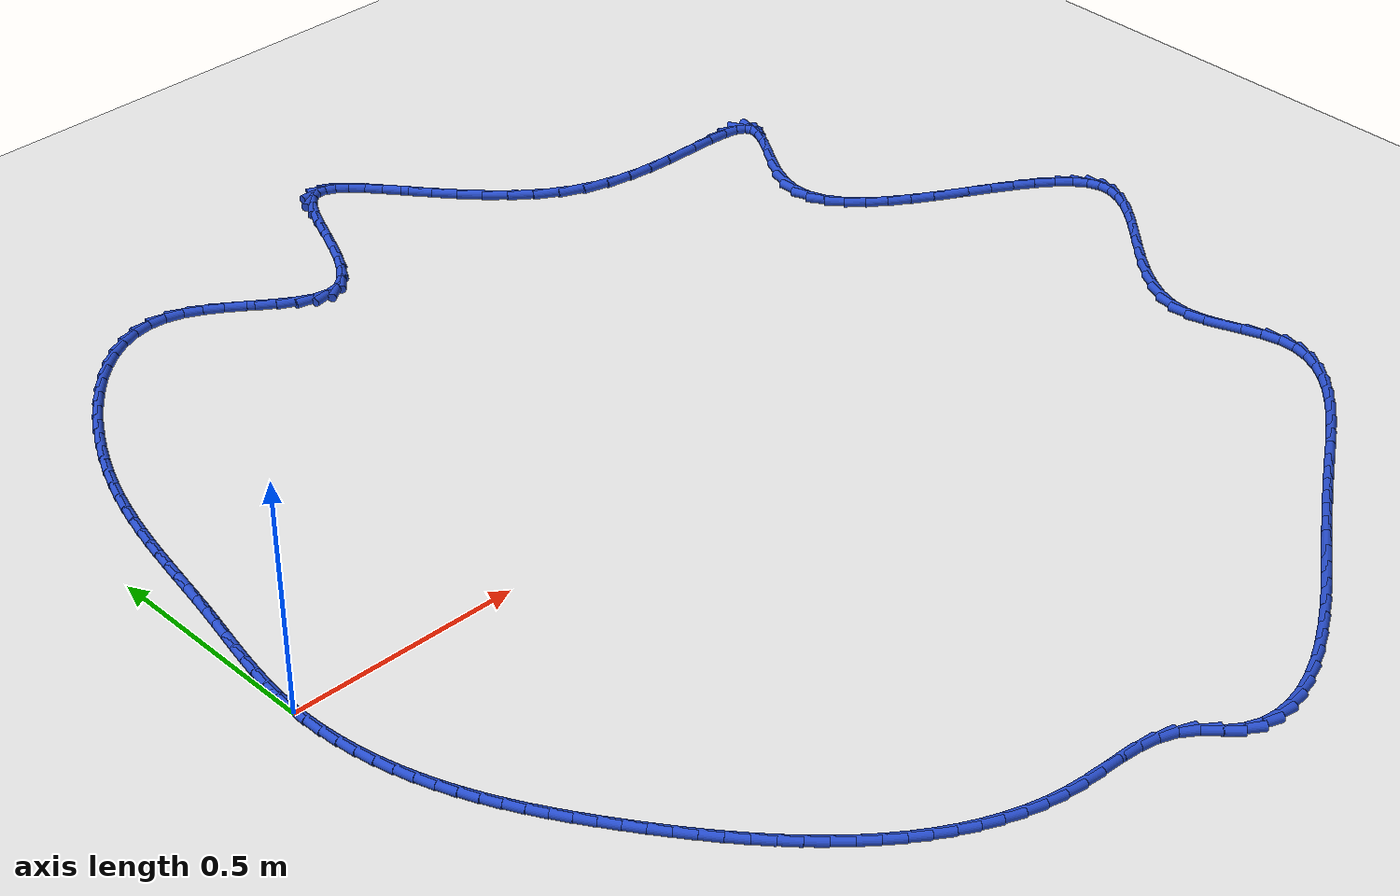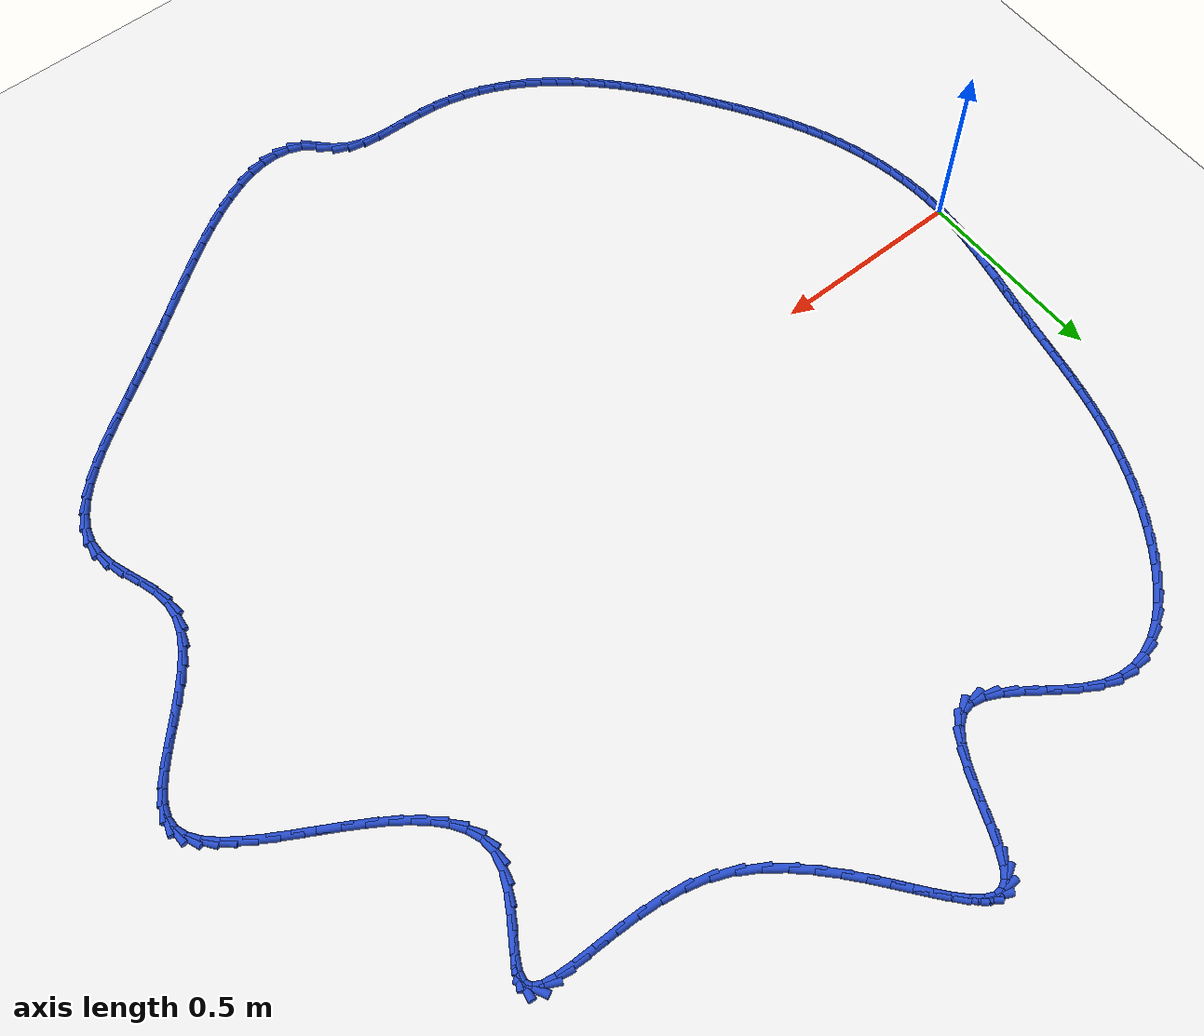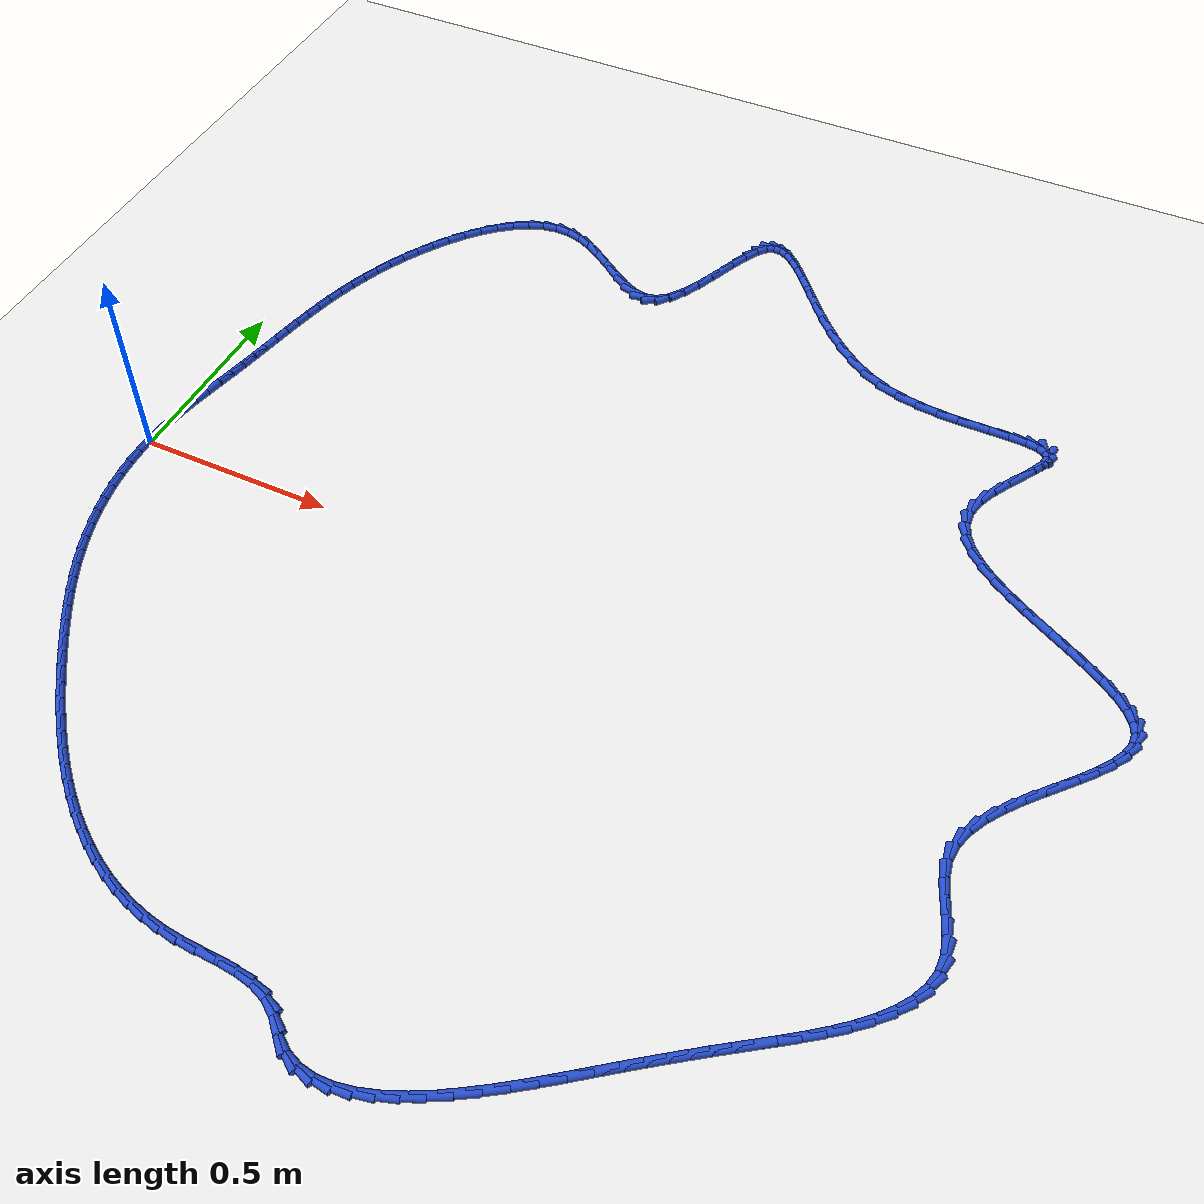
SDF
<sdf version="1.6">
 <world name="default">
  <light name="sun" type="directional">
   <pose>0 0 10 0 -0 0</pose>
   <diffuse>0.8 0.8 0.8 1</diffuse>
   <specular>0.2 0.2 0.2 1</specular>
   <attenuation>
    <range>1000</range>
    <constant>0.9</constant>
    <linear>0.01</linear>
    <quadratic>0.001</quadratic>
   </attenuation>
   <direction>-0.5 0.1 -0.9</direction>
  </light>
  <model name="ground_plane">
   <static>1</static>
   <link name="link">
    <collision name="collision">
     <geometry><plane><normal>0 0 1</normal><size>100 100</size></plane></geometry>
     <surface><friction><ode><mu>100</mu><mu2>50</mu2></ode></friction></surface>
    </collision>
    <visual name="visual">
     <cast_shadows>0</cast_shadows>
     <geometry><plane><normal>0 0 1</normal><size>100 100</size></plane></geometry>
     <material>
      <script><uri>file://media/materials/scripts/gazebo.material</uri><name>Gazebo/WhiteGlow</name></script>
     </material>
    </visual>
   </link>
  </model>
  <gravity>0 0 -9.8</gravity>
  <magnetic_field>6e-06 2.3e-05 -4.2e-05</magnetic_field>
  <atmosphere type="adiabatic"/>
  <physics name="default_physics" default="0" type="ode">
   <max_step_size>0.001</max_step_size>
   <real_time_factor>1</real_time_factor>
   <real_time_update_rate>1000</real_time_update_rate>
  </physics>
  <scene><ambient>0.4 0.4 0.4 1</ambient><background>0.7 0.7 0.7 1</background><shadows>1</shadows></scene>
  <spherical_coordinates>
   <surface_model>EARTH_WGS84</surface_model>
   <latitude_deg>0</latitude_deg>
   <longitude_deg>0</longitude_deg>
   <elevation>0</elevation>
   <heading_deg>0</heading_deg>
  </spherical_coordinates>
  <model name="line">
   <link name="link_0">
    <pose>-1.3877787807814457e-17 6.938893903907228e-18 0.01 0 1.57 1.5076179601624589</pose>
    <collision name="collision">
     <geometry><cylinder><radius>0.01</radius><length>0.08</length></cylinder></geometry>
    </collision>
    <visual name="visual">
     <material>
      <script><name>Gazebo/Blue</name><uri>file://media/materials/scripts/gazebo.material</uri></script>
     </material>
     <geometry><cylinder><radius>0.01</radius><length>0.08</length></cylinder></geometry>
    </visual>
   </link>
   <link name="link_1">
    <pose>0.0026327551362451125 0.041616323085471835 0.01 0 1.57 1.4605868004483655</pose>
    <collision name="collision">
     <geometry><cylinder><radius>0.01</radius><length>0.08</length></cylinder></geometry>
    </collision>
    <visual name="visual">
     <material>
      <script><name>Gazebo/Blue</name><uri>file://media/materials/scripts/gazebo.material</uri></script>
     </material>
     <geometry><cylinder><radius>0.01</radius><length>0.08</length></cylinder></geometry>
    </visual>
   </link>
   <link name="link_2">
    <pose>0.007219254293357643 0.08306387154017866 0.01 0 1.57 1.4224987146371908</pose>
    <collision name="collision">
     <geometry><cylinder><radius>0.01</radius><length>0.08</length></cylinder></geometry>
    </collision>
    <visual name="visual">
     <material>
      <script><name>Gazebo/Blue</name><uri>file://media/materials/scripts/gazebo.material</uri></script>
     </material>
     <geometry><cylinder><radius>0.01</radius><length>0.08</length></cylinder></geometry>
    </visual>
   </link>
   <link name="link_3">
    <pose>0.013383954649306378 0.12432847542178009 0.01 0 1.57 1.3932881311233953</pose>
    <collision name="collision">
     <geometry><cylinder><radius>0.01</radius><length>0.08</length></cylinder></geometry>
    </collision>
    <visual name="visual">
     <material>
      <script><name>Gazebo/Blue</name><uri>file://media/materials/scripts/gazebo.material</uri></script>
     </material>
     <geometry><cylinder><radius>0.01</radius><length>0.08</length></cylinder></geometry>
    </visual>
   </link>
   <link name="link_4">
    <pose>0.02075131338206009 0.16539596478793556 0.01 0 1.57 1.3728540379417484</pose>
    <collision name="collision">
     <geometry><cylinder><radius>0.01</radius><length>0.08</length></cylinder></geometry>
    </collision>
    <visual name="visual">
     <material>
      <script><name>Gazebo/Blue</name><uri>file://media/materials/scripts/gazebo.material</uri></script>
     </material>
     <geometry><cylinder><radius>0.01</radius><length>0.08</length></cylinder></geometry>
    </visual>
   </link>
   <link name="link_5">
    <pose>0.02894578766958756 0.2062521696963046 0.01 0 1.57 1.3611280731720357</pose>
    <collision name="collision">
     <geometry><cylinder><radius>0.01</radius><length>0.08</length></cylinder></geometry>
    </collision>
    <visual name="visual">
     <material>
      <script><name>Gazebo/Blue</name><uri>file://media/materials/scripts/gazebo.material</uri></script>
     </material>
     <geometry><cylinder><radius>0.01</radius><length>0.08</length></cylinder></geometry>
    </visual>
   </link>
   <link name="link_6">
    <pose>0.0375918346898576 0.24688292020454689 0.01 0 1.57 1.3581214666338204</pose>
    <collision name="collision">
     <geometry><cylinder><radius>0.01</radius><length>0.08</length></cylinder></geometry>
    </collision>
    <visual name="visual">
     <material>
      <script><name>Gazebo/Blue</name><uri>file://media/materials/scripts/gazebo.material</uri></script>
     </material>
     <geometry><cylinder><radius>0.01</radius><length>0.08</length></cylinder></geometry>
    </visual>
   </link>
   <link name="link_7">
    <pose>0.04631391162083896 0.2872740463703218 0.01 0 1.57 1.363953154609393</pose>
    <collision name="collision">
     <geometry><cylinder><radius>0.01</radius><length>0.08</length></cylinder></geometry>
    </collision>
    <visual name="visual">
     <material>
      <script><name>Gazebo/Blue</name><uri>file://media/materials/scripts/gazebo.material</uri></script>
     </material>
     <geometry><cylinder><radius>0.01</radius><length>0.08</length></cylinder></geometry>
    </visual>
   </link>
   <link name="link_8">
    <pose>0.054736507099724524 0.3274113816478101 0.01 0 1.57 1.3759581262300205</pose>
    <collision name="collision">
     <geometry><cylinder><radius>0.01</radius><length>0.08</length></cylinder></geometry>
    </collision>
    <visual name="visual">
     <material>
      <script><name>Gazebo/Blue</name><uri>file://media/materials/scripts/gazebo.material</uri></script>
     </material>
     <geometry><cylinder><radius>0.01</radius><length>0.08</length></cylinder></geometry>
    </visual>
   </link>
   <link name="link_9">
    <pose>0.06260701658135871 0.3672940292276096 0.01 0 1.57 1.384738151761699</pose>
    <collision name="collision">
     <geometry><cylinder><radius>0.01</radius><length>0.08</length></cylinder></geometry>
    </collision>
    <visual name="visual">
     <material>
      <script><name>Gazebo/Blue</name><uri>file://media/materials/scripts/gazebo.material</uri></script>
     </material>
     <geometry><cylinder><radius>0.01</radius><length>0.08</length></cylinder></geometry>
    </visual>
   </link>
   <link name="link_10">
    <pose>0.07007438913279483 0.40696444636881773 0.01 0 1.57 1.3882119774970212</pose>
    <collision name="collision">
     <geometry><cylinder><radius>0.01</radius><length>0.08</length></cylinder></geometry>
    </collision>
    <visual name="visual">
     <material>
      <script><name>Gazebo/Blue</name><uri>file://media/materials/scripts/gazebo.material</uri></script>
     </material>
     <geometry><cylinder><radius>0.01</radius><length>0.08</length></cylinder></geometry>
    </visual>
   </link>
   <link name="link_11">
    <pose>0.07736944847023469 0.446473929994874 0.01 0 1.57 1.3862797304278913</pose>
    <collision name="collision">
     <geometry><cylinder><radius>0.01</radius><length>0.08</length></cylinder></geometry>
    </collision>
    <visual name="visual">
     <material>
      <script><name>Gazebo/Blue</name><uri>file://media/materials/scripts/gazebo.material</uri></script>
     </material>
     <geometry><cylinder><radius>0.01</radius><length>0.08</length></cylinder></geometry>
    </visual>
   </link>
   <link name="link_12">
    <pose>0.08472301830988012 0.4858737770292177 0.01 0 1.57 1.3789156836017862</pose>
    <collision name="collision">
     <geometry><cylinder><radius>0.01</radius><length>0.08</length></cylinder></geometry>
    </collision>
    <visual name="visual">
     <material>
      <script><name>Gazebo/Blue</name><uri>file://media/materials/scripts/gazebo.material</uri></script>
     </material>
     <geometry><cylinder><radius>0.01</radius><length>0.08</length></cylinder></geometry>
    </visual>
   </link>
   <link name="link_13">
    <pose>0.09236592236793296 0.5252152843952888 0.01 0 1.57 1.366171451836873</pose>
    <collision name="collision">
     <geometry><cylinder><radius>0.01</radius><length>0.08</length></cylinder></geometry>
    </collision>
    <visual name="visual">
     <material>
      <script><name>Gazebo/Blue</name><uri>file://media/materials/scripts/gazebo.material</uri></script>
     </material>
     <geometry><cylinder><radius>0.01</radius><length>0.08</length></cylinder></geometry>
    </visual>
   </link>
   <link name="link_14">
    <pose>0.10052898436059504 0.5645497490165267 0.01 0 1.57 1.3481811065946365</pose>
    <collision name="collision">
     <geometry><cylinder><radius>0.01</radius><length>0.08</length></cylinder></geometry>
    </collision>
    <visual name="visual">
     <material>
      <script><name>Gazebo/Blue</name><uri>file://media/materials/scripts/gazebo.material</uri></script>
     </material>
     <geometry><cylinder><radius>0.01</radius><length>0.08</length></cylinder></geometry>
    </visual>
   </link>
   <link name="link_15">
    <pose>0.10944302800406827 0.6039284678163712 0.01 0 1.57 1.3251673017870698</pose>
    <collision name="collision">
     <geometry><cylinder><radius>0.01</radius><length>0.08</length></cylinder></geometry>
    </collision>
    <visual name="visual">
     <material>
      <script><name>Gazebo/Blue</name><uri>file://media/materials/scripts/gazebo.material</uri></script>
     </material>
     <geometry><cylinder><radius>0.01</radius><length>0.08</length></cylinder></geometry>
    </visual>
   </link>
   <link name="link_16">
    <pose>0.11933887701455442 0.6434027377182618 0.01 0 1.57 1.2974467726669479</pose>
    <collision name="collision">
     <geometry><cylinder><radius>0.01</radius><length>0.08</length></cylinder></geometry>
    </collision>
    <visual name="visual">
     <material>
      <script><name>Gazebo/Blue</name><uri>file://media/materials/scripts/gazebo.material</uri></script>
     </material>
     <geometry><cylinder><radius>0.01</radius><length>0.08</length></cylinder></geometry>
    </visual>
   </link>
   <link name="link_17">
    <pose>0.1304473551082554 0.6830238556456383 0.01 0 1.57 1.265433024340191</pose>
    <collision name="collision">
     <geometry><cylinder><radius>0.01</radius><length>0.08</length></cylinder></geometry>
    </collision>
    <visual name="visual">
     <material>
      <script><name>Gazebo/Blue</name><uri>file://media/materials/scripts/gazebo.material</uri></script>
     </material>
     <geometry><cylinder><radius>0.01</radius><length>0.08</length></cylinder></geometry>
    </visual>
   </link>
   <link name="link_18">
    <pose>0.14299928600137293 0.7228431185219399 0.01 0 1.57 1.2296338511295346</pose>
    <collision name="collision">
     <geometry><cylinder><radius>0.01</radius><length>0.08</length></cylinder></geometry>
    </collision>
    <visual name="visual">
     <material>
      <script><name>Gazebo/Blue</name><uri>file://media/materials/scripts/gazebo.material</uri></script>
     </material>
     <geometry><cylinder><radius>0.01</radius><length>0.08</length></cylinder></geometry>
    </visual>
   </link>
   <link name="link_19">
    <pose>0.15722549341010894 0.7629118232706067 0.01 0 1.57 1.1906417028819094</pose>
    <collision name="collision">
     <geometry><cylinder><radius>0.01</radius><length>0.08</length></cylinder></geometry>
    </collision>
    <visual name="visual">
     <material>
      <script><name>Gazebo/Blue</name><uri>file://media/materials/scripts/gazebo.material</uri></script>
     </material>
     <geometry><cylinder><radius>0.01</radius><length>0.08</length></cylinder></geometry>
    </visual>
   </link>
   <link name="link_20">
    <pose>0.1733568010506653 0.8032812668150782 0.01 0 1.57 1.1491159196537508</pose>
    <collision name="collision">
     <geometry><cylinder><radius>0.01</radius><length>0.08</length></cylinder></geometry>
    </collision>
    <visual name="visual">
     <material>
      <script><name>Gazebo/Blue</name><uri>file://media/materials/scripts/gazebo.material</uri></script>
     </material>
     <geometry><cylinder><radius>0.01</radius><length>0.08</length></cylinder></geometry>
    </visual>
   </link>
   <link name="link_21">
    <pose>0.19162403263924385 0.8440027460787939 0.01 0 1.57 1.1057573735704194</pose>
    <collision name="collision">
     <geometry><cylinder><radius>0.01</radius><length>0.08</length></cylinder></geometry>
    </collision>
    <visual name="visual">
     <material>
      <script><name>Gazebo/Blue</name><uri>file://media/materials/scripts/gazebo.material</uri></script>
     </material>
     <geometry><cylinder><radius>0.01</radius><length>0.08</length></cylinder></geometry>
    </visual>
   </link>
   <link name="link_22">
    <pose>0.2122580118920463 0.8851275579851934 0.01 0 1.57 1.061177169240294</pose>
    <collision name="collision">
     <geometry><cylinder><radius>0.01</radius><length>0.08</length></cylinder></geometry>
    </collision>
    <visual name="visual">
     <material>
      <script><name>Gazebo/Blue</name><uri>file://media/materials/scripts/gazebo.material</uri></script>
     </material>
     <geometry><cylinder><radius>0.01</radius><length>0.08</length></cylinder></geometry>
    </visual>
   </link>
   <link name="link_23">
    <pose>0.2354688289096542 0.9266600813192621 0.01 0 1.57 1.014197760810383</pose>
    <collision name="collision">
     <geometry><cylinder><radius>0.01</radius><length>0.08</length></cylinder></geometry>
    </collision>
    <visual name="visual">
     <material>
      <script><name>Gazebo/Blue</name><uri>file://media/materials/scripts/gazebo.material</uri></script>
     </material>
     <geometry><cylinder><radius>0.01</radius><length>0.08</length></cylinder></geometry>
    </visual>
   </link>
   <link name="link_24">
    <pose>0.26121883924322 0.9680440958801244 0.01 0 1.57 0.9622163802211118</pose>
    <collision name="collision">
     <geometry><cylinder><radius>0.01</radius><length>0.08</length></cylinder></geometry>
    </collision>
    <visual name="visual">
     <material>
      <script><name>Gazebo/Blue</name><uri>file://media/materials/scripts/gazebo.material</uri></script>
     </material>
     <geometry><cylinder><radius>0.01</radius><length>0.08</length></cylinder></geometry>
    </visual>
   </link>
   <link name="link_25">
    <pose>0.2893073265799867 1.0083543658340808 0.01 0 1.57 0.9027844205554127</pose>
    <collision name="collision">
     <geometry><cylinder><radius>0.01</radius><length>0.08</length></cylinder></geometry>
    </collision>
    <visual name="visual">
     <material>
      <script><name>Gazebo/Blue</name><uri>file://media/materials/scripts/gazebo.material</uri></script>
     </material>
     <geometry><cylinder><radius>0.01</radius><length>0.08</length></cylinder></geometry>
    </visual>
   </link>
   <link name="link_26">
    <pose>0.31953070725112087 1.0466591668018799 0.01 0 1.57 0.8329453561516905</pose>
    <collision name="collision">
     <geometry><cylinder><radius>0.01</radius><length>0.08</length></cylinder></geometry>
    </collision>
    <visual name="visual">
     <material>
      <script><name>Gazebo/Blue</name><uri>file://media/materials/scripts/gazebo.material</uri></script>
     </material>
     <geometry><cylinder><radius>0.01</radius><length>0.08</length></cylinder></geometry>
    </visual>
   </link>
   <link name="link_27">
    <pose>0.3516853975877889 1.0820267744042702 0.01 0 1.57 0.7489553550305024</pose>
    <collision name="collision">
     <geometry><cylinder><radius>0.01</radius><length>0.08</length></cylinder></geometry>
    </collision>
    <visual name="visual">
     <material>
      <script><name>Gazebo/Blue</name><uri>file://media/materials/scripts/gazebo.material</uri></script>
     </material>
     <geometry><cylinder><radius>0.01</radius><length>0.08</length></cylinder></geometry>
    </visual>
   </link>
   <link name="link_28">
    <pose>0.38556781392115735 1.1135254642620007 0.01 0 1.57 0.6460832516018167</pose>
    <collision name="collision">
     <geometry><cylinder><radius>0.01</radius><length>0.08</length></cylinder></geometry>
    </collision>
    <visual name="visual">
     <material>
      <script><name>Gazebo/Blue</name><uri>file://media/materials/scripts/gazebo.material</uri></script>
     </material>
     <geometry><cylinder><radius>0.01</radius><length>0.08</length></cylinder></geometry>
    </visual>
   </link>
   <link name="link_29">
    <pose>0.4209743725823928 1.1402235119958195 0.01 0 1.57 0.5187099812458319</pose>
    <collision name="collision">
     <geometry><cylinder><radius>0.01</radius><length>0.08</length></cylinder></geometry>
    </collision>
    <visual name="visual">
     <material>
      <script><name>Gazebo/Blue</name><uri>file://media/materials/scripts/gazebo.material</uri></script>
     </material>
     <geometry><cylinder><radius>0.01</radius><length>0.08</length></cylinder></geometry>
    </visual>
   </link>
   <link name="link_30">
    <pose>0.45770148990266124 1.1611891932264757 0.01 0 1.57 0.3613178272862656</pose>
    <collision name="collision">
     <geometry><cylinder><radius>0.01</radius><length>0.08</length></cylinder></geometry>
    </collision>
    <visual name="visual">
     <material>
      <script><name>Gazebo/Blue</name><uri>file://media/materials/scripts/gazebo.material</uri></script>
     </material>
     <geometry><cylinder><radius>0.01</radius><length>0.08</length></cylinder></geometry>
    </visual>
   </link>
   <link name="link_31">
    <pose>0.4955455822131299 1.1754907835747186 0.01 0 1.57 0.17132273776619258</pose>
    <collision name="collision">
     <geometry><cylinder><radius>0.01</radius><length>0.08</length></cylinder></geometry>
    </collision>
    <visual name="visual">
     <material>
      <script><name>Gazebo/Blue</name><uri>file://media/materials/scripts/gazebo.material</uri></script>
     </material>
     <geometry><cylinder><radius>0.01</radius><length>0.08</length></cylinder></geometry>
    </visual>
   </link>
   <link name="link_32">
    <pose>0.5343030658449643 1.1821965586612957 0.01 0 1.57 -0.04612610356052276</pose>
    <collision name="collision">
     <geometry><cylinder><radius>0.01</radius><length>0.08</length></cylinder></geometry>
    </collision>
    <visual name="visual">
     <material>
      <script><name>Gazebo/Blue</name><uri>file://media/materials/scripts/gazebo.material</uri></script>
     </material>
     <geometry><cylinder><radius>0.01</radius><length>0.08</length></cylinder></geometry>
    </visual>
   </link>
   <link name="link_33">
    <pose>0.5737703571293319 1.1803747941069567 0.01 0 1.57 -0.27423346381484426</pose>
    <collision name="collision">
     <geometry><cylinder><radius>0.01</radius><length>0.08</length></cylinder></geometry>
    </collision>
    <visual name="visual">
     <material>
      <script><name>Gazebo/Blue</name><uri>file://media/materials/scripts/gazebo.material</uri></script>
     </material>
     <geometry><cylinder><radius>0.01</radius><length>0.08</length></cylinder></geometry>
    </visual>
   </link>
   <link name="link_34">
    <pose>0.613741920430834 1.1691299445251104 0.01 0 1.57 -0.46064967516766686</pose>
    <collision name="collision">
     <geometry><cylinder><radius>0.01</radius><length>0.08</length></cylinder></geometry>
    </collision>
    <visual name="visual">
     <material>
      <script><name>Gazebo/Blue</name><uri>file://media/materials/scripts/gazebo.material</uri></script>
     </material>
     <geometry><cylinder><radius>0.01</radius><length>0.08</length></cylinder></geometry>
    </visual>
   </link>
   <link name="link_35">
    <pose>0.6539246837381176 1.1491889195243044 0.01 0 1.57 -0.5707539028939539</pose>
    <collision name="collision">
     <geometry><cylinder><radius>0.01</radius><length>0.08</length></cylinder></geometry>
    </collision>
    <visual name="visual">
     <material>
      <script><name>Gazebo/Blue</name><uri>file://media/materials/scripts/gazebo.material</uri></script>
     </material>
     <geometry><cylinder><radius>0.01</radius><length>0.08</length></cylinder></geometry>
    </visual>
   </link>
   <link name="link_36">
    <pose>0.6939046196394448 1.1235204932111964 0.01 0 1.57 -0.6228150052060327</pose>
    <collision name="collision">
     <geometry><cylinder><radius>0.01</radius><length>0.08</length></cylinder></geometry>
    </collision>
    <visual name="visual">
     <material>
      <script><name>Gazebo/Blue</name><uri>file://media/materials/scripts/gazebo.material</uri></script>
     </material>
     <geometry><cylinder><radius>0.01</radius><length>0.08</length></cylinder></geometry>
    </visual>
   </link>
   <link name="link_37">
    <pose>0.7332588450904327 1.095257575633189 0.01 0 1.57 -0.6265020345457875</pose>
    <collision name="collision">
     <geometry><cylinder><radius>0.01</radius><length>0.08</length></cylinder></geometry>
    </collision>
    <visual name="visual">
     <material>
      <script><name>Gazebo/Blue</name><uri>file://media/materials/scripts/gazebo.material</uri></script>
     </material>
     <geometry><cylinder><radius>0.01</radius><length>0.08</length></cylinder></geometry>
    </visual>
   </link>
   <link name="link_38">
    <pose>0.7715644770466997 1.0675330768376834 0.01 0 1.57 -0.5784901718930553</pose>
    <collision name="collision">
     <geometry><cylinder><radius>0.01</radius><length>0.08</length></cylinder></geometry>
    </collision>
    <visual name="visual">
     <material>
      <script><name>Gazebo/Blue</name><uri>file://media/materials/scripts/gazebo.material</uri></script>
     </material>
     <geometry><cylinder><radius>0.01</radius><length>0.08</length></cylinder></geometry>
    </visual>
   </link>
   <link name="link_39">
    <pose>0.8083986324638647 1.0434799068720815 0.01 0 1.57 -0.4585754483207538</pose>
    <collision name="collision">
     <geometry><cylinder><radius>0.01</radius><length>0.08</length></cylinder></geometry>
    </collision>
    <visual name="visual">
     <material>
      <script><name>Gazebo/Blue</name><uri>file://media/materials/scripts/gazebo.material</uri></script>
     </material>
     <geometry><cylinder><radius>0.01</radius><length>0.08</length></cylinder></geometry>
    </visual>
   </link>
   <link name="link_40">
    <pose>0.843338428297545 1.0262309757837849 0.01 0 1.57 -0.22048881653023114</pose>
    <collision name="collision">
     <geometry><cylinder><radius>0.01</radius><length>0.08</length></cylinder></geometry>
    </collision>
    <visual name="visual">
     <material>
      <script><name>Gazebo/Blue</name><uri>file://media/materials/scripts/gazebo.material</uri></script>
     </material>
     <geometry><cylinder><radius>0.01</radius><length>0.08</length></cylinder></geometry>
    </visual>
   </link>
   <link name="link_41">
    <pose>0.8759609815033594 1.0189191936201951 0.01 0 1.57 0.18958945562480917</pose>
    <collision name="collision">
     <geometry><cylinder><radius>0.01</radius><length>0.08</length></cylinder></geometry>
    </collision>
    <visual name="visual">
     <material>
      <script><name>Gazebo/Blue</name><uri>file://media/materials/scripts/gazebo.material</uri></script>
     </material>
     <geometry><cylinder><radius>0.01</radius><length>0.08</length></cylinder></geometry>
    </visual>
   </link>
   <link name="link_42">
    <pose>0.905846587933181 1.0246540664240622 0.01 0 1.57 0.6322822355981306</pose>
    <collision name="collision">
     <geometry><cylinder><radius>0.01</radius><length>0.08</length></cylinder></geometry>
    </collision>
    <visual name="visual">
     <material>
      <script><name>Gazebo/Blue</name><uri>file://media/materials/scripts/gazebo.material</uri></script>
     </material>
     <geometry><cylinder><radius>0.01</radius><length>0.08</length></cylinder></geometry>
    </visual>
   </link>
   <link name="link_43">
    <pose>0.9328607805464052 1.0444450975783952 0.01 0 1.57 0.9035906401974453</pose>
    <collision name="collision">
     <geometry><cylinder><radius>0.01</radius><length>0.08</length></cylinder></geometry>
    </collision>
    <visual name="visual">
     <material>
      <script><name>Gazebo/Blue</name><uri>file://media/materials/scripts/gazebo.material</uri></script>
     </material>
     <geometry><cylinder><radius>0.01</radius><length>0.08</length></cylinder></geometry>
    </visual>
   </link>
   <link name="link_44">
    <pose>0.9573763223565704 1.0755674079657898 0.01 0 1.57 1.0524252334753903</pose>
    <collision name="collision">
     <geometry><cylinder><radius>0.01</radius><length>0.08</length></cylinder></geometry>
    </collision>
    <visual name="visual">
     <material>
      <script><name>Gazebo/Blue</name><uri>file://media/materials/scripts/gazebo.material</uri></script>
     </material>
     <geometry><cylinder><radius>0.01</radius><length>0.08</length></cylinder></geometry>
    </visual>
   </link>
   <link name="link_45">
    <pose>0.9798182201458758 1.1149114838955188 0.01 0 1.57 1.1333018410664129</pose>
    <collision name="collision">
     <geometry><cylinder><radius>0.01</radius><length>0.08</length></cylinder></geometry>
    </collision>
    <visual name="visual">
     <material>
      <script><name>Gazebo/Blue</name><uri>file://media/materials/scripts/gazebo.material</uri></script>
     </material>
     <geometry><cylinder><radius>0.01</radius><length>0.08</length></cylinder></geometry>
    </visual>
   </link>
   <link name="link_46">
    <pose>1.0006114806965225 1.1593678116768582 0.01 0 1.57 1.17212912287952</pose>
    <collision name="collision">
     <geometry><cylinder><radius>0.01</radius><length>0.08</length></cylinder></geometry>
    </collision>
    <visual name="visual">
     <material>
      <script><name>Gazebo/Blue</name><uri>file://media/materials/scripts/gazebo.material</uri></script>
     </material>
     <geometry><cylinder><radius>0.01</radius><length>0.08</length></cylinder></geometry>
    </visual>
   </link>
   <link name="link_47">
    <pose>1.02018111079071 1.2058268776190812 0.01 0 1.57 1.1783706883098528</pose>
    <collision name="collision">
     <geometry><cylinder><radius>0.01</radius><length>0.08</length></cylinder></geometry>
    </collision>
    <visual name="visual">
     <material>
      <script><name>Gazebo/Blue</name><uri>file://media/materials/scripts/gazebo.material</uri></script>
     </material>
     <geometry><cylinder><radius>0.01</radius><length>0.08</length></cylinder></geometry>
    </visual>
   </link>
   <link name="link_48">
    <pose>1.0389521172106395 1.2511791680314632 0.01 0 1.57 1.150245571902516</pose>
    <collision name="collision">
     <geometry><cylinder><radius>0.01</radius><length>0.08</length></cylinder></geometry>
    </collision>
    <visual name="visual">
     <material>
      <script><name>Gazebo/Blue</name><uri>file://media/materials/scripts/gazebo.material</uri></script>
     </material>
     <geometry><cylinder><radius>0.01</radius><length>0.08</length></cylinder></geometry>
    </visual>
   </link>
   <link name="link_49">
    <pose>1.0573495067385108 1.2923151692232775 0.01 0 1.57 1.0712934029688055</pose>
    <collision name="collision">
     <geometry><cylinder><radius>0.01</radius><length>0.08</length></cylinder></geometry>
    </collision>
    <visual name="visual">
     <material>
      <script><name>Gazebo/Blue</name><uri>file://media/materials/scripts/gazebo.material</uri></script>
     </material>
     <geometry><cylinder><radius>0.01</radius><length>0.08</length></cylinder></geometry>
    </visual>
   </link>
   <link name="link_50">
    <pose>1.0757982861565247 1.3261253675037996 0.01 0 1.57 0.8902815790380342</pose>
    <collision name="collision">
     <geometry><cylinder><radius>0.01</radius><length>0.08</length></cylinder></geometry>
    </collision>
    <visual name="visual">
     <material>
      <script><name>Gazebo/Blue</name><uri>file://media/materials/scripts/gazebo.material</uri></script>
     </material>
     <geometry><cylinder><radius>0.01</radius><length>0.08</length></cylinder></geometry>
    </visual>
   </link>
   <link name="link_51">
    <pose>1.0947232876188209 1.349503620108984 0.01 0 1.57 0.5084205048175772</pose>
    <collision name="collision">
     <geometry><cylinder><radius>0.01</radius><length>0.08</length></cylinder></geometry>
    </collision>
    <visual name="visual">
     <material>
      <script><name>Gazebo/Blue</name><uri>file://media/materials/scripts/gazebo.material</uri></script>
     </material>
     <geometry><cylinder><radius>0.01</radius><length>0.08</length></cylinder></geometry>
    </visual>
   </link>
   <link name="link_52">
    <pose>1.1144884877789316 1.360518506312133 0.01 0 1.57 -0.01853033949895068</pose>
    <collision name="collision">
     <geometry><cylinder><radius>0.01</radius><length>0.08</length></cylinder></geometry>
    </collision>
    <visual name="visual">
     <material>
      <script><name>Gazebo/Blue</name><uri>file://media/materials/scripts/gazebo.material</uri></script>
     </material>
     <geometry><cylinder><radius>0.01</radius><length>0.08</length></cylinder></geometry>
    </visual>
   </link>
   <link name="link_53">
    <pose>1.1353079386399603 1.3601326706565746 0.01 0 1.57 -0.4399393017097629</pose>
    <collision name="collision">
     <geometry><cylinder><radius>0.01</radius><length>0.08</length></cylinder></geometry>
    </collision>
    <visual name="visual">
     <material>
      <script><name>Gazebo/Blue</name><uri>file://media/materials/scripts/gazebo.material</uri></script>
     </material>
     <geometry><cylinder><radius>0.01</radius><length>0.08</length></cylinder></geometry>
    </visual>
   </link>
   <link name="link_54">
    <pose>1.1573730154166388 1.3497464982804928 0.01 0 1.57 -0.6795084681212601</pose>
    <collision name="collision">
     <geometry><cylinder><radius>0.01</radius><length>0.08</length></cylinder></geometry>
    </collision>
    <visual name="visual">
     <material>
      <script><name>Gazebo/Blue</name><uri>file://media/materials/scripts/gazebo.material</uri></script>
     </material>
     <geometry><cylinder><radius>0.01</radius><length>0.08</length></cylinder></geometry>
    </visual>
   </link>
   <link name="link_55">
    <pose>1.1808750933236998 1.3307603743220735 0.01 0 1.57 -0.8059586996184304</pose>
    <collision name="collision">
     <geometry><cylinder><radius>0.01</radius><length>0.08</length></cylinder></geometry>
    </collision>
    <visual name="visual">
     <material>
      <script><name>Gazebo/Blue</name><uri>file://media/materials/scripts/gazebo.material</uri></script>
     </material>
     <geometry><cylinder><radius>0.01</radius><length>0.08</length></cylinder></geometry>
    </visual>
   </link>
   <link name="link_56">
    <pose>1.2060055475758737 1.3045746839195005 0.01 0 1.57 -0.8706185802185191</pose>
    <collision name="collision">
     <geometry><cylinder><radius>0.01</radius><length>0.08</length></cylinder></geometry>
    </collision>
    <visual name="visual">
     <material>
      <script><name>Gazebo/Blue</name><uri>file://media/materials/scripts/gazebo.material</uri></script>
     </material>
     <geometry><cylinder><radius>0.01</radius><length>0.08</length></cylinder></geometry>
    </visual>
   </link>
   <link name="link_57">
    <pose>1.2329557533878939 1.27258981221096 0.01 0 1.57 -0.8985003004416768</pose>
    <collision name="collision">
     <geometry><cylinder><radius>0.01</radius><length>0.08</length></cylinder></geometry>
    </collision>
    <visual name="visual">
     <material>
      <script><name>Gazebo/Blue</name><uri>file://media/materials/scripts/gazebo.material</uri></script>
     </material>
     <geometry><cylinder><radius>0.01</radius><length>0.08</length></cylinder></geometry>
    </visual>
   </link>
   <link name="link_58">
    <pose>1.2619170859744915 1.236206144334635 0.01 0 1.57 -0.9013703994362381</pose>
    <collision name="collision">
     <geometry><cylinder><radius>0.01</radius><length>0.08</length></cylinder></geometry>
    </collision>
    <visual name="visual">
     <material>
      <script><name>Gazebo/Blue</name><uri>file://media/materials/scripts/gazebo.material</uri></script>
     </material>
     <geometry><cylinder><radius>0.01</radius><length>0.08</length></cylinder></geometry>
    </visual>
   </link>
   <link name="link_59">
    <pose>1.2930809205503984 1.1968240654287126 0.01 0 1.57 -0.8846498576630334</pose>
    <collision name="collision">
     <geometry><cylinder><radius>0.01</radius><length>0.08</length></cylinder></geometry>
    </collision>
    <visual name="visual">
     <material>
      <script><name>Gazebo/Blue</name><uri>file://media/materials/scripts/gazebo.material</uri></script>
     </material>
     <geometry><cylinder><radius>0.01</radius><length>0.08</length></cylinder></geometry>
    </visual>
   </link>
   <link name="link_60">
    <pose>1.3266386323303467 1.1558439606313753 0.01 0 1.57 -0.8504219265182946</pose>
    <collision name="collision">
     <geometry><cylinder><radius>0.01</radius><length>0.08</length></cylinder></geometry>
    </collision>
    <visual name="visual">
     <material>
      <script><name>Gazebo/Blue</name><uri>file://media/materials/scripts/gazebo.material</uri></script>
     </material>
     <geometry><cylinder><radius>0.01</radius><length>0.08</length></cylinder></geometry>
    </visual>
   </link>
   <link name="link_61">
    <pose>1.3627815965290686 1.1146662150808089 0.01 0 1.57 -0.7987748263929947</pose>
    <collision name="collision">
     <geometry><cylinder><radius>0.01</radius><length>0.08</length></cylinder></geometry>
    </collision>
    <visual name="visual">
     <material>
      <script><name>Gazebo/Blue</name><uri>file://media/materials/scripts/gazebo.material</uri></script>
     </material>
     <geometry><cylinder><radius>0.01</radius><length>0.08</length></cylinder></geometry>
    </visual>
   </link>
   <link name="link_62">
    <pose>1.4017011883612958 1.0746912139151985 0.01 0 1.57 -0.7284857630693855</pose>
    <collision name="collision">
     <geometry><cylinder><radius>0.01</radius><length>0.08</length></cylinder></geometry>
    </collision>
    <visual name="visual">
     <material>
      <script><name>Gazebo/Blue</name><uri>file://media/materials/scripts/gazebo.material</uri></script>
     </material>
     <geometry><cylinder><radius>0.01</radius><length>0.08</length></cylinder></geometry>
    </visual>
   </link>
   <link name="link_63">
    <pose>1.4435887830417595 1.037319342272729 0.01 0 1.57 -0.6375520809514028</pose>
    <collision name="collision">
     <geometry><cylinder><radius>0.01</radius><length>0.08</length></cylinder></geometry>
    </collision>
    <visual name="visual">
     <material>
      <script><name>Gazebo/Blue</name><uri>file://media/materials/scripts/gazebo.material</uri></script>
     </material>
     <geometry><cylinder><radius>0.01</radius><length>0.08</length></cylinder></geometry>
    </visual>
   </link>
   <link name="link_64">
    <pose>1.4886357557851924 1.0039509852915844 0.01 0 1.57 -0.5239398974846688</pose>
    <collision name="collision">
     <geometry><cylinder><radius>0.01</radius><length>0.08</length></cylinder></geometry>
    </collision>
    <visual name="visual">
     <material>
      <script><name>Gazebo/Blue</name><uri>file://media/materials/scripts/gazebo.material</uri></script>
     </material>
     <geometry><cylinder><radius>0.01</radius><length>0.08</length></cylinder></geometry>
    </visual>
   </link>
   <link name="link_65">
    <pose>1.537033481806326 0.9759865281099498 0.01 0 1.57 -0.3872040263620928</pose>
    <collision name="collision">
     <geometry><cylinder><radius>0.01</radius><length>0.08</length></cylinder></geometry>
    </collision>
    <visual name="visual">
     <material>
      <script><name>Gazebo/Blue</name><uri>file://media/materials/scripts/gazebo.material</uri></script>
     </material>
     <geometry><cylinder><radius>0.01</radius><length>0.08</length></cylinder></geometry>
    </visual>
   </link>
   <link name="link_66">
    <pose>1.588963045525703 0.9548101578093429 0.01 0 1.57 -0.2503834632655432</pose>
    <collision name="collision">
     <geometry><cylinder><radius>0.01</radius><length>0.08</length></cylinder></geometry>
    </collision>
    <visual name="visual">
     <material>
      <script><name>Gazebo/Blue</name><uri>file://media/materials/scripts/gazebo.material</uri></script>
     </material>
     <geometry><cylinder><radius>0.01</radius><length>0.08</length></cylinder></geometry>
    </visual>
   </link>
   <link name="link_67">
    <pose>1.6439352374642586 0.9407509962964729 0.01 0 1.57 -0.14593731203825155</pose>
    <collision name="collision">
     <geometry><cylinder><radius>0.01</radius><length>0.08</length></cylinder></geometry>
    </collision>
    <visual name="visual">
     <material>
      <script><name>Gazebo/Blue</name><uri>file://media/materials/scripts/gazebo.material</uri></script>
     </material>
     <geometry><cylinder><radius>0.01</radius><length>0.08</length></cylinder></geometry>
    </visual>
   </link>
   <link name="link_68">
    <pose>1.7003903099313558 0.9324531022751995 0.01 0 1.57 -0.07171975302223485</pose>
    <collision name="collision">
     <geometry><cylinder><radius>0.01</radius><length>0.08</length></cylinder></geometry>
    </collision>
    <visual name="visual">
     <material>
      <script><name>Gazebo/Blue</name><uri>file://media/materials/scripts/gazebo.material</uri></script>
     </material>
     <geometry><cylinder><radius>0.01</radius><length>0.08</length></cylinder></geometry>
    </visual>
   </link>
   <link name="link_69">
    <pose>1.7566726330871485 0.9284096127170234 0.01 0 1.57 -0.023794484662976397</pose>
    <collision name="collision">
     <geometry><cylinder><radius>0.01</radius><length>0.08</length></cylinder></geometry>
    </collision>
    <visual name="visual">
     <material>
      <script><name>Gazebo/Blue</name><uri>file://media/materials/scripts/gazebo.material</uri></script>
     </material>
     <geometry><cylinder><radius>0.01</radius><length>0.08</length></cylinder></geometry>
    </visual>
   </link>
   <link name="link_70">
    <pose>1.8111265770917895 0.9271136645934445 0.01 0 1.57 -0.001084358765670592</pose>
    <collision name="collision">
     <geometry><cylinder><radius>0.01</radius><length>0.08</length></cylinder></geometry>
    </collision>
    <visual name="visual">
     <material>
      <script><name>Gazebo/Blue</name><uri>file://media/materials/scripts/gazebo.material</uri></script>
     </material>
     <geometry><cylinder><radius>0.01</radius><length>0.08</length></cylinder></geometry>
    </visual>
   </link>
   <link name="link_71">
    <pose>1.862096512105434 0.9270583948759641 0.01 0 1.57 -0.00701389900016491</pose>
    <collision name="collision">
     <geometry><cylinder><radius>0.01</radius><length>0.08</length></cylinder></geometry>
    </collision>
    <visual name="visual">
     <material>
      <script><name>Gazebo/Blue</name><uri>file://media/materials/scripts/gazebo.material</uri></script>
     </material>
     <geometry><cylinder><radius>0.01</radius><length>0.08</length></cylinder></geometry>
    </visual>
   </link>
   <link name="link_72">
    <pose>1.9079268082882335 0.9267369405360812 0.01 0 1.57 -0.053605582346749295</pose>
    <collision name="collision">
     <geometry><cylinder><radius>0.01</radius><length>0.08</length></cylinder></geometry>
    </collision>
    <visual name="visual">
     <material>
      <script><name>Gazebo/Blue</name><uri>file://media/materials/scripts/gazebo.material</uri></script>
     </material>
     <geometry><cylinder><radius>0.01</radius><length>0.08</length></cylinder></geometry>
    </visual>
   </link>
   <link name="link_73">
    <pose>1.9469618358003413 0.924642438545297 0.01 0 1.57 -0.17394956293932287</pose>
    <collision name="collision">
     <geometry><cylinder><radius>0.01</radius><length>0.08</length></cylinder></geometry>
    </collision>
    <visual name="visual">
     <material>
      <script><name>Gazebo/Blue</name><uri>file://media/materials/scripts/gazebo.material</uri></script>
     </material>
     <geometry><cylinder><radius>0.01</radius><length>0.08</length></cylinder></geometry>
    </visual>
   </link>
   <link name="link_74">
    <pose>1.9775459648019114 0.9192680258751119 0.01 0 1.57 -0.4606108643305508</pose>
    <collision name="collision">
     <geometry><cylinder><radius>0.01</radius><length>0.08</length></cylinder></geometry>
    </collision>
    <visual name="visual">
     <material>
      <script><name>Gazebo/Blue</name><uri>file://media/materials/scripts/gazebo.material</uri></script>
     </material>
     <geometry><cylinder><radius>0.01</radius><length>0.08</length></cylinder></geometry>
    </visual>
   </link>
   <link name="link_75">
    <pose>1.9980235654530967 0.9091068394970256 0.01 0 1.57 -1.0837041318186138</pose>
    <collision name="collision">
     <geometry><cylinder><radius>0.01</radius><length>0.08</length></cylinder></geometry>
    </collision>
    <visual name="visual">
     <material>
      <script><name>Gazebo/Blue</name><uri>file://media/materials/scripts/gazebo.material</uri></script>
     </material>
     <geometry><cylinder><radius>0.01</radius><length>0.08</length></cylinder></geometry>
    </visual>
   </link>
   <link name="link_76">
    <pose>2.00673900791405 0.8926520163825393 0.01 0 1.57 1.3905420031865883</pose>
    <collision name="collision">
     <geometry><cylinder><radius>0.01</radius><length>0.08</length></cylinder></geometry>
    </collision>
    <visual name="visual">
     <material>
      <script><name>Gazebo/Blue</name><uri>file://media/materials/scripts/gazebo.material</uri></script>
     </material>
     <geometry><cylinder><radius>0.01</radius><length>0.08</length></cylinder></geometry>
    </visual>
   </link>
   <link name="link_77">
    <pose>2.0023509477732206 0.8685725284272752 0.01 0 1.57 1.110391089515679</pose>
    <collision name="collision">
     <geometry><cylinder><radius>0.01</radius><length>0.08</length></cylinder></geometry>
    </collision>
    <visual name="visual">
     <material>
      <script><name>Gazebo/Blue</name><uri>file://media/materials/scripts/gazebo.material</uri></script>
     </material>
     <geometry><cylinder><radius>0.01</radius><length>0.08</length></cylinder></geometry>
    </visual>
   </link>
   <link name="link_78">
    <pose>1.9869075242880554 0.8374336798098557 0.01 0 1.57 1.0204106189087272</pose>
    <collision name="collision">
     <geometry><cylinder><radius>0.01</radius><length>0.08</length></cylinder></geometry>
    </collision>
    <visual name="visual">
     <material>
      <script><name>Gazebo/Blue</name><uri>file://media/materials/scripts/gazebo.material</uri></script>
     </material>
     <geometry><cylinder><radius>0.01</radius><length>0.08</length></cylinder></geometry>
    </visual>
   </link>
   <link name="link_79">
    <pose>1.9645244422428072 0.8009575264854523 0.01 0 1.57 1.009854492019791</pose>
    <collision name="collision">
     <geometry><cylinder><radius>0.01</radius><length>0.08</length></cylinder></geometry>
    </collision>
    <visual name="visual">
     <material>
      <script><name>Gazebo/Blue</name><uri>file://media/materials/scripts/gazebo.material</uri></script>
     </material>
     <geometry><cylinder><radius>0.01</radius><length>0.08</length></cylinder></geometry>
    </visual>
   </link>
   <link name="link_80">
    <pose>1.9393468857153253 0.7608826173449126 0.01 0 1.57 1.054099810068853</pose>
    <collision name="collision">
     <geometry><cylinder><radius>0.01</radius><length>0.08</length></cylinder></geometry>
    </collision>
    <visual name="visual">
     <material>
      <script><name>Gazebo/Blue</name><uri>file://media/materials/scripts/gazebo.material</uri></script>
     </material>
     <geometry><cylinder><radius>0.01</radius><length>0.08</length></cylinder></geometry>
    </visual>
   </link>
   <link name="link_81">
    <pose>1.9155200387834583 0.7189475012790825 0.01 0 1.57 1.159761486048604</pose>
    <collision name="collision">
     <geometry><cylinder><radius>0.01</radius><length>0.08</length></cylinder></geometry>
    </collision>
    <visual name="visual">
     <material>
      <script><name>Gazebo/Blue</name><uri>file://media/materials/scripts/gazebo.material</uri></script>
     </material>
     <geometry><cylinder><radius>0.01</radius><length>0.08</length></cylinder></geometry>
    </visual>
   </link>
   <link name="link_82">
    <pose>1.8971890855250564 0.6768907271788104 0.01 0 1.57 1.3580167006771908</pose>
    <collision name="collision">
     <geometry><cylinder><radius>0.01</radius><length>0.08</length></cylinder></geometry>
    </collision>
    <visual name="visual">
     <material>
      <script><name>Gazebo/Blue</name><uri>file://media/materials/scripts/gazebo.material</uri></script>
     </material>
     <geometry><cylinder><radius>0.01</radius><length>0.08</length></cylinder></geometry>
    </visual>
   </link>
   <link name="link_83">
    <pose>1.888448097451912 0.636432569768431 0.01 0 1.57 -1.4993212457243625</pose>
    <collision name="collision">
     <geometry><cylinder><radius>0.01</radius><length>0.08</length></cylinder></geometry>
    </collision>
    <visual name="visual">
     <material>
      <script><name>Gazebo/Blue</name><uri>file://media/materials/scripts/gazebo.material</uri></script>
     </material>
     <geometry><cylinder><radius>0.01</radius><length>0.08</length></cylinder></geometry>
    </visual>
   </link>
   <link name="link_84">
    <pose>1.89116416526539 0.5984970960822681 0.01 0 1.57 -1.2204454963079903</pose>
    <collision name="collision">
     <geometry><cylinder><radius>0.01</radius><length>0.08</length></cylinder></geometry>
    </collision>
    <visual name="visual">
     <material>
      <script><name>Gazebo/Blue</name><uri>file://media/materials/scripts/gazebo.material</uri></script>
     </material>
     <geometry><cylinder><radius>0.01</radius><length>0.08</length></cylinder></geometry>
    </visual>
   </link>
   <link name="link_85">
    <pose>1.9041644167840388 0.5629215017216694 0.01 0 1.57 -0.9913584666370526</pose>
    <collision name="collision">
     <geometry><cylinder><radius>0.01</radius><length>0.08</length></cylinder></geometry>
    </collision>
    <visual name="visual">
     <material>
      <script><name>Gazebo/Blue</name><uri>file://media/materials/scripts/gazebo.material</uri></script>
     </material>
     <geometry><cylinder><radius>0.01</radius><length>0.08</length></cylinder></geometry>
    </visual>
   </link>
   <link name="link_86">
    <pose>1.9260573185859673 0.5294648048019757 0.01 0 1.57 -0.8212145996162292</pose>
    <collision name="collision">
     <geometry><cylinder><radius>0.01</radius><length>0.08</length></cylinder></geometry>
    </collision>
    <visual name="visual">
     <material>
      <script><name>Gazebo/Blue</name><uri>file://media/materials/scripts/gazebo.material</uri></script>
     </material>
     <geometry><cylinder><radius>0.01</radius><length>0.08</length></cylinder></geometry>
    </visual>
   </link>
   <link name="link_87">
    <pose>1.9554513372492857 0.49788602343852684 0.01 0 1.57 -0.7006188100497215</pose>
    <collision name="collision">
     <geometry><cylinder><radius>0.01</radius><length>0.08</length></cylinder></geometry>
    </collision>
    <visual name="visual">
     <material>
      <script><name>Gazebo/Blue</name><uri>file://media/materials/scripts/gazebo.material</uri></script>
     </material>
     <geometry><cylinder><radius>0.01</radius><length>0.08</length></cylinder></geometry>
    </visual>
   </link>
   <link name="link_88">
    <pose>1.9909549393521049 0.46794417574666436 0.01 0 1.57 -0.6172161538614971</pose>
    <collision name="collision">
     <geometry><cylinder><radius>0.01</radius><length>0.08</length></cylinder></geometry>
    </collision>
    <visual name="visual">
     <material>
      <script><name>Gazebo/Blue</name><uri>file://media/materials/scripts/gazebo.material</uri></script>
     </material>
     <geometry><cylinder><radius>0.01</radius><length>0.08</length></cylinder></geometry>
    </visual>
   </link>
   <link name="link_89">
    <pose>2.0311765914725335 0.4393982798417286 0.01 0 1.57 -0.5614562006738169</pose>
    <collision name="collision">
     <geometry><cylinder><radius>0.01</radius><length>0.08</length></cylinder></geometry>
    </collision>
    <visual name="visual">
     <material>
      <script><name>Gazebo/Blue</name><uri>file://media/materials/scripts/gazebo.material</uri></script>
     </material>
     <geometry><cylinder><radius>0.01</radius><length>0.08</length></cylinder></geometry>
    </visual>
   </link>
   <link name="link_90">
    <pose>2.0747247601886825 0.4120073538390606 0.01 0 1.57 -0.5271733754649587</pose>
    <collision name="collision">
     <geometry><cylinder><radius>0.01</radius><length>0.08</length></cylinder></geometry>
    </collision>
    <visual name="visual">
     <material>
      <script><name>Gazebo/Blue</name><uri>file://media/materials/scripts/gazebo.material</uri></script>
     </material>
     <geometry><cylinder><radius>0.01</radius><length>0.08</length></cylinder></geometry>
    </visual>
   </link>
   <link name="link_91">
    <pose>2.1202079120786625 0.3855304158540009 0.01 0 1.57 -0.5109684221987678</pose>
    <collision name="collision">
     <geometry><cylinder><radius>0.01</radius><length>0.08</length></cylinder></geometry>
    </collision>
    <visual name="visual">
     <material>
      <script><name>Gazebo/Blue</name><uri>file://media/materials/scripts/gazebo.material</uri></script>
     </material>
     <geometry><cylinder><radius>0.01</radius><length>0.08</length></cylinder></geometry>
    </visual>
   </link>
   <link name="link_92">
    <pose>2.166234513720583 0.3597264840018902 0.01 0 1.57 -0.5116996604804317</pose>
    <collision name="collision">
     <geometry><cylinder><radius>0.01</radius><length>0.08</length></cylinder></geometry>
    </collision>
    <visual name="visual">
     <material>
      <script><name>Gazebo/Blue</name><uri>file://media/materials/scripts/gazebo.material</uri></script>
     </material>
     <geometry><cylinder><radius>0.01</radius><length>0.08</length></cylinder></geometry>
    </visual>
   </link>
   <link name="link_93">
    <pose>2.211413031692553 0.3343545763980694 0.01 0 1.57 -0.5303853637165998</pose>
    <collision name="collision">
     <geometry><cylinder><radius>0.01</radius><length>0.08</length></cylinder></geometry>
    </collision>
    <visual name="visual">
     <material>
      <script><name>Gazebo/Blue</name><uri>file://media/materials/scripts/gazebo.material</uri></script>
     </material>
     <geometry><cylinder><radius>0.01</radius><length>0.08</length></cylinder></geometry>
    </visual>
   </link>
   <link name="link_94">
    <pose>2.2543519325726837 0.30917371115787906 0.01 0 1.57 -0.5706447908361542</pose>
    <collision name="collision">
     <geometry><cylinder><radius>0.01</radius><length>0.08</length></cylinder></geometry>
    </collision>
    <visual name="visual">
     <material>
      <script><name>Gazebo/Blue</name><uri>file://media/materials/scripts/gazebo.material</uri></script>
     </material>
     <geometry><cylinder><radius>0.01</radius><length>0.08</length></cylinder></geometry>
    </visual>
   </link>
   <link name="link_95">
    <pose>2.293659682939085 0.2839429063966598 0.01 0 1.57 -0.6399060140706834</pose>
    <collision name="collision">
     <geometry><cylinder><radius>0.01</radius><length>0.08</length></cylinder></geometry>
    </collision>
    <visual name="visual">
     <material>
      <script><name>Gazebo/Blue</name><uri>file://media/materials/scripts/gazebo.material</uri></script>
     </material>
     <geometry><cylinder><radius>0.01</radius><length>0.08</length></cylinder></geometry>
    </visual>
   </link>
   <link name="link_96">
    <pose>2.327944749369867 0.2584211802297527 0.01 0 1.57 -0.7517115663660293</pose>
    <collision name="collision">
     <geometry><cylinder><radius>0.01</radius><length>0.08</length></cylinder></geometry>
    </collision>
    <visual name="visual">
     <material>
      <script><name>Gazebo/Blue</name><uri>file://media/materials/scripts/gazebo.material</uri></script>
     </material>
     <geometry><cylinder><radius>0.01</radius><length>0.08</length></cylinder></geometry>
    </visual>
   </link>
   <link name="link_97">
    <pose>2.3558155984431397 0.23236755077249818 0.01 0 1.57 -0.9286035691986613</pose>
    <collision name="collision">
     <geometry><cylinder><radius>0.01</radius><length>0.08</length></cylinder></geometry>
    </collision>
    <visual name="visual">
     <material>
      <script><name>Gazebo/Blue</name><uri>file://media/materials/scripts/gazebo.material</uri></script>
     </material>
     <geometry><cylinder><radius>0.01</radius><length>0.08</length></cylinder></geometry>
    </visual>
   </link>
   <link name="link_98">
    <pose>2.375880696737013 0.20554103614023772 0.01 0 1.57 -1.1986264873676709</pose>
    <collision name="collision">
     <geometry><cylinder><radius>0.01</radius><length>0.08</length></cylinder></geometry>
    </collision>
    <visual name="visual">
     <material>
      <script><name>Gazebo/Blue</name><uri>file://media/materials/scripts/gazebo.material</uri></script>
     </material>
     <geometry><cylinder><radius>0.01</radius><length>0.08</length></cylinder></geometry>
    </visual>
   </link>
   <link name="link_99">
    <pose>2.386748510829597 0.17770065444831087 0.01 0 1.57 -1.5560571346839944</pose>
    <collision name="collision">
     <geometry><cylinder><radius>0.01</radius><length>0.08</length></cylinder></geometry>
    </collision>
    <visual name="visual">
     <material>
      <script><name>Gazebo/Blue</name><uri>file://media/materials/scripts/gazebo.material</uri></script>
     </material>
     <geometry><cylinder><radius>0.01</radius><length>0.08</length></cylinder></geometry>
    </visual>
   </link>
   <link name="link_100">
    <pose>2.3871771651647458 0.14862013967898033 0.01 0 1.57 1.268723361209941</pose>
    <collision name="collision">
     <geometry><cylinder><radius>0.01</radius><length>0.08</length></cylinder></geometry>
    </collision>
    <visual name="visual">
     <material>
      <script><name>Gazebo/Blue</name><uri>file://media/materials/scripts/gazebo.material</uri></script>
     </material>
     <geometry><cylinder><radius>0.01</radius><length>0.08</length></cylinder></geometry>
    </visual>
   </link>
   <link name="link_101">
    <pose>2.377713270984884 0.1182490878287614 0.01 0 1.57 1.0617903407687619</pose>
    <collision name="collision">
     <geometry><cylinder><radius>0.01</radius><length>0.08</length></cylinder></geometry>
    </collision>
    <visual name="visual">
     <material>
      <script><name>Gazebo/Blue</name><uri>file://media/materials/scripts/gazebo.material</uri></script>
     </material>
     <geometry><cylinder><radius>0.01</radius><length>0.08</length></cylinder></geometry>
    </visual>
   </link>
   <link name="link_102">
    <pose>2.360080862603273 0.08665287097539645 0.01 0 1.57 0.9373212739125154</pose>
    <collision name="collision">
     <geometry><cylinder><radius>0.01</radius><length>0.08</length></cylinder></geometry>
    </collision>
    <visual name="visual">
     <material>
      <script><name>Gazebo/Blue</name><uri>file://media/materials/scripts/gazebo.material</uri></script>
     </material>
     <geometry><cylinder><radius>0.01</radius><length>0.08</length></cylinder></geometry>
    </visual>
   </link>
   <link name="link_103">
    <pose>2.3360246842503707 0.0538988976040289 0.01 0 1.57 0.8668594878361183</pose>
    <collision name="collision">
     <geometry><cylinder><radius>0.01</radius><length>0.08</length></cylinder></geometry>
    </collision>
    <visual name="visual">
     <material>
      <script><name>Gazebo/Blue</name><uri>file://media/materials/scripts/gazebo.material</uri></script>
     </material>
     <geometry><cylinder><radius>0.01</radius><length>0.08</length></cylinder></geometry>
    </visual>
   </link>
   <link name="link_104">
    <pose>2.307289480156635 0.02005457619980225 0.01 0 1.57 0.8334215017022062</pose>
    <collision name="collision">
     <geometry><cylinder><radius>0.01</radius><length>0.08</length></cylinder></geometry>
    </collision>
    <visual name="visual">
     <material>
      <script><name>Gazebo/Blue</name><uri>file://media/materials/scripts/gazebo.material</uri></script>
     </material>
     <geometry><cylinder><radius>0.01</radius><length>0.08</length></cylinder></geometry>
    </visual>
   </link>
   <link name="link_105">
    <pose>2.2756199945525233 -0.01481268475213941 0.01 0 1.57 0.8285235753655876</pose>
    <collision name="collision">
     <geometry><cylinder><radius>0.01</radius><length>0.08</length></cylinder></geometry>
    </collision>
    <visual name="visual">
     <material>
      <script><name>Gazebo/Blue</name><uri>file://media/materials/scripts/gazebo.material</uri></script>
     </material>
     <geometry><cylinder><radius>0.01</radius><length>0.08</length></cylinder></geometry>
    </visual>
   </link>
   <link name="link_106">
    <pose>2.2427609716684938 -0.0506354767666541 0.01 0 1.57 0.8491689391609892</pose>
    <collision name="collision">
     <geometry><cylinder><radius>0.01</radius><length>0.08</length></cylinder></geometry>
    </collision>
    <visual name="visual">
     <material>
      <script><name>Gazebo/Blue</name><uri>file://media/materials/scripts/gazebo.material</uri></script>
     </material>
     <geometry><cylinder><radius>0.01</radius><length>0.08</length></cylinder></geometry>
    </visual>
   </link>
   <link name="link_107">
    <pose>2.210457155735002 -0.0873463913585976 0.01 0 1.57 0.8964037764036563</pose>
    <collision name="collision">
     <geometry><cylinder><radius>0.01</radius><length>0.08</length></cylinder></geometry>
    </collision>
    <visual name="visual">
     <material>
      <script><name>Gazebo/Blue</name><uri>file://media/materials/scripts/gazebo.material</uri></script>
     </material>
     <geometry><cylinder><radius>0.01</radius><length>0.08</length></cylinder></geometry>
    </visual>
   </link>
   <link name="link_108">
    <pose>2.1804532909825074 -0.1248780200428265 0.01 0 1.57 0.9749530563876075</pose>
    <collision name="collision">
     <geometry><cylinder><radius>0.01</radius><length>0.08</length></cylinder></geometry>
    </collision>
    <visual name="visual">
     <material>
      <script><name>Gazebo/Blue</name><uri>file://media/materials/scripts/gazebo.material</uri></script>
     </material>
     <geometry><cylinder><radius>0.01</radius><length>0.08</length></cylinder></geometry>
    </visual>
   </link>
   <link name="link_109">
    <pose>2.154494121641469 -0.16316295433419742 0.01 0 1.57 1.0931998869406676</pose>
    <collision name="collision">
     <geometry><cylinder><radius>0.01</radius><length>0.08</length></cylinder></geometry>
    </collision>
    <visual name="visual">
     <material>
      <script><name>Gazebo/Blue</name><uri>file://media/materials/scripts/gazebo.material</uri></script>
     </material>
     <geometry><cylinder><radius>0.01</radius><length>0.08</length></cylinder></geometry>
    </visual>
   </link>
   <link name="link_110">
    <pose>2.1343243919423425 -0.2021337857475668 0.01 0 1.57 1.2618505342738444</pose>
    <collision name="collision">
     <geometry><cylinder><radius>0.01</radius><length>0.08</length></cylinder></geometry>
    </collision>
    <visual name="visual">
     <material>
      <script><name>Gazebo/Blue</name><uri>file://media/materials/scripts/gazebo.material</uri></script>
     </material>
     <geometry><cylinder><radius>0.01</radius><length>0.08</length></cylinder></geometry>
    </visual>
   </link>
   <link name="link_111">
    <pose>2.1216888461155863 -0.24172310579779135 0.01 0 1.57 1.4873342575169683</pose>
    <collision name="collision">
     <geometry><cylinder><radius>0.01</radius><length>0.08</length></cylinder></geometry>
    </collision>
    <visual name="visual">
     <material>
      <script><name>Gazebo/Blue</name><uri>file://media/materials/scripts/gazebo.material</uri></script>
     </material>
     <geometry><cylinder><radius>0.01</radius><length>0.08</length></cylinder></geometry>
    </visual>
   </link>
   <link name="link_112">
    <pose>2.1183308499970526 -0.28186343960520477 0.01 0 1.57 -1.4150505301382823</pose>
    <collision name="collision">
     <geometry><cylinder><radius>0.01</radius><length>0.08</length></cylinder></geometry>
    </collision>
    <visual name="visual">
     <material>
      <script><name>Gazebo/Blue</name><uri>file://media/materials/scripts/gazebo.material</uri></script>
     </material>
     <geometry><cylinder><radius>0.01</radius><length>0.08</length></cylinder></geometry>
    </visual>
   </link>
   <link name="link_113">
    <pose>2.1246997189865677 -0.32242498045888146 0.01 0 1.57 -1.2648171659036167</pose>
    <collision name="collision">
     <geometry><cylinder><radius>0.01</radius><length>0.08</length></cylinder></geometry>
    </collision>
    <visual name="visual">
     <material>
      <script><name>Gazebo/Blue</name><uri>file://media/materials/scripts/gazebo.material</uri></script>
     </material>
     <geometry><cylinder><radius>0.01</radius><length>0.08</length></cylinder></geometry>
    </visual>
   </link>
   <link name="link_114">
    <pose>2.1375489165708284 -0.36309989982478236 0.01 0 1.57 -1.2064211673489724</pose>
    <collision name="collision">
     <geometry><cylinder><radius>0.01</radius><length>0.08</length></cylinder></geometry>
    </collision>
    <visual name="visual">
     <material>
      <script><name>Gazebo/Blue</name><uri>file://media/materials/scripts/gazebo.material</uri></script>
     </material>
     <geometry><cylinder><radius>0.01</radius><length>0.08</length></cylinder></geometry>
    </visual>
   </link>
   <link name="link_115">
    <pose>2.152976373413753 -0.4035487934588669 0.01 0 1.57 -1.2308989544645683</pose>
    <collision name="collision">
     <geometry><cylinder><radius>0.01</radius><length>0.08</length></cylinder></geometry>
    </collision>
    <visual name="visual">
     <material>
      <script><name>Gazebo/Blue</name><uri>file://media/materials/scripts/gazebo.material</uri></script>
     </material>
     <geometry><cylinder><radius>0.01</radius><length>0.08</length></cylinder></geometry>
    </visual>
   </link>
   <link name="link_116">
    <pose>2.1670800201792626 -0.4434322571170949 0.01 0 1.57 -1.346856563586588</pose>
    <collision name="collision">
     <geometry><cylinder><radius>0.01</radius><length>0.08</length></cylinder></geometry>
    </collision>
    <visual name="visual">
     <material>
      <script><name>Gazebo/Blue</name><uri>file://media/materials/scripts/gazebo.material</uri></script>
     </material>
     <geometry><cylinder><radius>0.01</radius><length>0.08</length></cylinder></geometry>
    </visual>
   </link>
   <link name="link_117">
    <pose>2.175957787531275 -0.48241088655542563 0.01 0 1.57 -1.5677325985430732</pose>
    <collision name="collision">
     <geometry><cylinder><radius>0.01</radius><length>0.08</length></cylinder></geometry>
    </collision>
    <visual name="visual">
     <material>
      <script><name>Gazebo/Blue</name><uri>file://media/materials/scripts/gazebo.material</uri></script>
     </material>
     <geometry><cylinder><radius>0.01</radius><length>0.08</length></cylinder></geometry>
    </visual>
   </link>
   <link name="link_118">
    <pose>2.1760734694313926 -0.520169306579134 0.01 0 1.57 1.3279155796091364</pose>
    <collision name="collision">
     <geometry><cylinder><radius>0.01</radius><length>0.08</length></cylinder></geometry>
    </collision>
    <visual name="visual">
     <material>
      <script><name>Gazebo/Blue</name><uri>file://media/materials/scripts/gazebo.material</uri></script>
     </material>
     <geometry><cylinder><radius>0.01</radius><length>0.08</length></cylinder></geometry>
    </visual>
   </link>
   <link name="link_119">
    <pose>2.1670470985862735 -0.5565994364035607 0.01 0 1.57 1.1212581006713946</pose>
    <collision name="collision">
     <geometry><cylinder><radius>0.01</radius><length>0.08</length></cylinder></geometry>
    </collision>
    <visual name="visual">
     <material>
      <script><name>Gazebo/Blue</name><uri>file://media/materials/scripts/gazebo.material</uri></script>
     </material>
     <geometry><cylinder><radius>0.01</radius><length>0.08</length></cylinder></geometry>
    </visual>
   </link>
   <link name="link_120">
    <pose>2.1501119889779017 -0.5916991518009619 0.01 0 1.57 0.9608671922395416</pose>
    <collision name="collision">
     <geometry><cylinder><radius>0.01</radius><length>0.08</length></cylinder></geometry>
    </collision>
    <visual name="visual">
     <material>
      <script><name>Gazebo/Blue</name><uri>file://media/materials/scripts/gazebo.material</uri></script>
     </material>
     <geometry><cylinder><radius>0.01</radius><length>0.08</length></cylinder></geometry>
    </visual>
   </link>
   <link name="link_121">
    <pose>2.1265144379985776 -0.6254671812637467 0.01 0 1.57 0.8410192646304357</pose>
    <collision name="collision">
     <geometry><cylinder><radius>0.01</radius><length>0.08</length></cylinder></geometry>
    </collision>
    <visual name="visual">
     <material>
      <script><name>Gazebo/Blue</name><uri>file://media/materials/scripts/gazebo.material</uri></script>
     </material>
     <geometry><cylinder><radius>0.01</radius><length>0.08</length></cylinder></geometry>
    </visual>
   </link>
   <link name="link_122">
    <pose>2.097500743040606 -0.6579022532843242 0.01 0 1.57 0.7530112898569726</pose>
    <collision name="collision">
     <geometry><cylinder><radius>0.01</radius><length>0.08</length></cylinder></geometry>
    </collision>
    <visual name="visual">
     <material>
      <script><name>Gazebo/Blue</name><uri>file://media/materials/scripts/gazebo.material</uri></script>
     </material>
     <geometry><cylinder><radius>0.01</radius><length>0.08</length></cylinder></geometry>
    </visual>
   </link>
   <link name="link_123">
    <pose>2.0643172014962863 -0.6890030963551034 0.01 0 1.57 0.6894207846304432</pose>
    <collision name="collision">
     <geometry><cylinder><radius>0.01</radius><length>0.08</length></cylinder></geometry>
    </collision>
    <visual name="visual">
     <material>
      <script><name>Gazebo/Blue</name><uri>file://media/materials/scripts/gazebo.material</uri></script>
     </material>
     <geometry><cylinder><radius>0.01</radius><length>0.08</length></cylinder></geometry>
    </visual>
   </link>
   <link name="link_124">
    <pose>2.0282101107579202 -0.7187684389684929 0.01 0 1.57 0.6450291097352489</pose>
    <collision name="collision">
     <geometry><cylinder><radius>0.01</radius><length>0.08</length></cylinder></geometry>
    </collision>
    <visual name="visual">
     <material>
      <script><name>Gazebo/Blue</name><uri>file://media/materials/scripts/gazebo.material</uri></script>
     </material>
     <geometry><cylinder><radius>0.01</radius><length>0.08</length></cylinder></geometry>
    </visual>
   </link>
   <link name="link_125">
    <pose>1.9904257682178121 -0.7471970096169016 0.01 0 1.57 0.6166690080853638</pose>
    <collision name="collision">
     <geometry><cylinder><radius>0.01</radius><length>0.08</length></cylinder></geometry>
    </collision>
    <visual name="visual">
     <material>
      <script><name>Gazebo/Blue</name><uri>file://media/materials/scripts/gazebo.material</uri></script>
     </material>
     <geometry><cylinder><radius>0.01</radius><length>0.08</length></cylinder></geometry>
    </visual>
   </link>
   <link name="link_126">
    <pose>1.9522104712682613 -0.7742875367927397 0.01 0 1.57 0.6029904511512321</pose>
    <collision name="collision">
     <geometry><cylinder><radius>0.01</radius><length>0.08</length></cylinder></geometry>
    </collision>
    <visual name="visual">
     <material>
      <script><name>Gazebo/Blue</name><uri>file://media/materials/scripts/gazebo.material</uri></script>
     </material>
     <geometry><cylinder><radius>0.01</radius><length>0.08</length></cylinder></geometry>
    </visual>
   </link>
   <link name="link_127">
    <pose>1.9148105173015693 -0.800038748988415 0.01 0 1.57 0.6030071920287059</pose>
    <collision name="collision">
     <geometry><cylinder><radius>0.01</radius><length>0.08</length></cylinder></geometry>
    </collision>
    <visual name="visual">
     <material>
      <script><name>Gazebo/Blue</name><uri>file://media/materials/scripts/gazebo.material</uri></script>
     </material>
     <geometry><cylinder><radius>0.01</radius><length>0.08</length></cylinder></geometry>
    </visual>
   </link>
   <link name="link_128">
    <pose>1.879288865542419 -0.8244975592141944 0.01 0 1.57 0.60800319354592</pose>
    <collision name="collision">
     <geometry><cylinder><radius>0.01</radius><length>0.08</length></cylinder></geometry>
    </collision>
    <visual name="visual">
     <material>
      <script><name>Gazebo/Blue</name><uri>file://media/materials/scripts/gazebo.material</uri></script>
     </material>
     <geometry><cylinder><radius>0.01</radius><length>0.08</length></cylinder></geometry>
    </visual>
   </link>
   <link name="link_129">
    <pose>1.8454641157342522 -0.8480379201929327 0.01 0 1.57 0.6138529279818523</pose>
    <collision name="collision">
     <geometry><cylinder><radius>0.01</radius><length>0.08</length></cylinder></geometry>
    </collision>
    <visual name="visual">
     <material>
      <script><name>Gazebo/Blue</name><uri>file://media/materials/scripts/gazebo.material</uri></script>
     </material>
     <geometry><cylinder><radius>0.01</radius><length>0.08</length></cylinder></geometry>
    </visual>
   </link>
   <link name="link_130">
    <pose>1.8126376678601914 -0.8711697139054799 0.01 0 1.57 0.6202282509569338</pose>
    <collision name="collision">
     <geometry><cylinder><radius>0.01</radius><length>0.08</length></cylinder></geometry>
    </collision>
    <visual name="visual">
     <material>
      <script><name>Gazebo/Blue</name><uri>file://media/materials/scripts/gazebo.material</uri></script>
     </material>
     <geometry><cylinder><radius>0.01</radius><length>0.08</length></cylinder></geometry>
    </visual>
   </link>
   <link name="link_131">
    <pose>1.7801092349537249 -0.8944032656929313 0.01 0 1.57 0.6267282131596057</pose>
    <collision name="collision">
     <geometry><cylinder><radius>0.01</radius><length>0.08</length></cylinder></geometry>
    </collision>
    <visual name="visual">
     <material>
      <script><name>Gazebo/Blue</name><uri>file://media/materials/scripts/gazebo.material</uri></script>
     </material>
     <geometry><cylinder><radius>0.01</radius><length>0.08</length></cylinder></geometry>
    </visual>
   </link>
   <link name="link_132">
    <pose>1.7471785300483427 -0.9182489008963808 0.01 0 1.57 0.6329459404361825</pose>
    <collision name="collision">
     <geometry><cylinder><radius>0.01</radius><length>0.08</length></cylinder></geometry>
    </collision>
    <visual name="visual">
     <material>
      <script><name>Gazebo/Blue</name><uri>file://media/materials/scripts/gazebo.material</uri></script>
     </material>
     <geometry><cylinder><radius>0.01</radius><length>0.08</length></cylinder></geometry>
    </visual>
   </link>
   <link name="link_133">
    <pose>1.7131452661775324 -0.9432169448569243 0.01 0 1.57 0.6385289949351992</pose>
    <collision name="collision">
     <geometry><cylinder><radius>0.01</radius><length>0.08</length></cylinder></geometry>
    </collision>
    <visual name="visual">
     <material>
      <script><name>Gazebo/Blue</name><uri>file://media/materials/scripts/gazebo.material</uri></script>
     </material>
     <geometry><cylinder><radius>0.01</radius><length>0.08</length></cylinder></geometry>
    </visual>
   </link>
   <link name="link_134">
    <pose>1.6773114704593257 -0.9698149334768281 0.01 0 1.57 0.6407024947586776</pose>
    <collision name="collision">
     <geometry><cylinder><radius>0.01</radius><length>0.08</length></cylinder></geometry>
    </collision>
    <visual name="visual">
     <material>
      <script><name>Gazebo/Blue</name><uri>file://media/materials/scripts/gazebo.material</uri></script>
     </material>
     <geometry><cylinder><radius>0.01</radius><length>0.08</length></cylinder></geometry>
    </visual>
   </link>
   <link name="link_135">
    <pose>1.6393130546463712 -0.9981479321580468 0.01 0 1.57 0.6349048582789478</pose>
    <collision name="collision">
     <geometry><cylinder><radius>0.01</radius><length>0.08</length></cylinder></geometry>
    </collision>
    <visual name="visual">
     <material>
      <script><name>Gazebo/Blue</name><uri>file://media/materials/scripts/gazebo.material</uri></script>
     </material>
     <geometry><cylinder><radius>0.01</radius><length>0.08</length></cylinder></geometry>
    </visual>
   </link>
   <link name="link_136">
    <pose>1.5994655970084426 -1.027501724146859 0.01 0 1.57 0.6212426379238899</pose>
    <collision name="collision">
     <geometry><cylinder><radius>0.01</radius><length>0.08</length></cylinder></geometry>
    </collision>
    <visual name="visual">
     <material>
      <script><name>Gazebo/Blue</name><uri>file://media/materials/scripts/gazebo.material</uri></script>
     </material>
     <geometry><cylinder><radius>0.01</radius><length>0.08</length></cylinder></geometry>
    </visual>
   </link>
   <link name="link_137">
    <pose>1.558167305215936 -1.0570624897346308 0.01 0 1.57 0.5996798136069784</pose>
    <collision name="collision">
     <geometry><cylinder><radius>0.01</radius><length>0.08</length></cylinder></geometry>
    </collision>
    <visual name="visual">
     <material>
      <script><name>Gazebo/Blue</name><uri>file://media/materials/scripts/gazebo.material</uri></script>
     </material>
     <geometry><cylinder><radius>0.01</radius><length>0.08</length></cylinder></geometry>
    </visual>
   </link>
   <link name="link_138">
    <pose>1.5158163869392463 -1.086016409212726 0.01 0 1.57 0.569475461764689</pose>
    <collision name="collision">
     <geometry><cylinder><radius>0.01</radius><length>0.08</length></cylinder></geometry>
    </collision>
    <visual name="visual">
     <material>
      <script><name>Gazebo/Blue</name><uri>file://media/materials/scripts/gazebo.material</uri></script>
     </material>
     <geometry><cylinder><radius>0.01</radius><length>0.08</length></cylinder></geometry>
    </visual>
   </link>
   <link name="link_139">
    <pose>1.4728110498487705 -1.11354966287251 0.01 0 1.57 0.5291579692595917</pose>
    <collision name="collision">
     <geometry><cylinder><radius>0.01</radius><length>0.08</length></cylinder></geometry>
    </collision>
    <visual name="visual">
     <material>
      <script><name>Gazebo/Blue</name><uri>file://media/materials/scripts/gazebo.material</uri></script>
     </material>
     <geometry><cylinder><radius>0.01</radius><length>0.08</length></cylinder></geometry>
    </visual>
   </link>
   <link name="link_140">
    <pose>1.4295495016149027 -1.1388484310053477 0.01 0 1.57 0.4763797038067081</pose>
    <collision name="collision">
     <geometry><cylinder><radius>0.01</radius><length>0.08</length></cylinder></geometry>
    </collision>
    <visual name="visual">
     <material>
      <script><name>Gazebo/Blue</name><uri>file://media/materials/scripts/gazebo.material</uri></script>
     </material>
     <geometry><cylinder><radius>0.01</radius><length>0.08</length></cylinder></geometry>
    </visual>
   </link>
   <link name="link_141">
    <pose>1.3864299499080386 -1.161098893902604 0.01 0 1.57 0.407667165331636</pose>
    <collision name="collision">
     <geometry><cylinder><radius>0.01</radius><length>0.08</length></cylinder></geometry>
    </collision>
    <visual name="visual">
     <material>
      <script><name>Gazebo/Blue</name><uri>file://media/materials/scripts/gazebo.material</uri></script>
     </material>
     <geometry><cylinder><radius>0.01</radius><length>0.08</length></cylinder></geometry>
    </visual>
   </link>
   <link name="link_142">
    <pose>1.343850602398574 -1.1794872318556429 0.01 0 1.57 0.31811689192727804</pose>
    <collision name="collision">
     <geometry><cylinder><radius>0.01</radius><length>0.08</length></cylinder></geometry>
    </collision>
    <visual name="visual">
     <material>
      <script><name>Gazebo/Blue</name><uri>file://media/materials/scripts/gazebo.material</uri></script>
     </material>
     <geometry><cylinder><radius>0.01</radius><length>0.08</length></cylinder></geometry>
    </visual>
   </link>
   <link name="link_143">
    <pose>1.3022096667569043 -1.1931996251558306 0.01 0 1.57 0.20125180256979674</pose>
    <collision name="collision">
     <geometry><cylinder><radius>0.01</radius><length>0.08</length></cylinder></geometry>
    </collision>
    <visual name="visual">
     <material>
      <script><name>Gazebo/Blue</name><uri>file://media/materials/scripts/gazebo.material</uri></script>
     </material>
     <geometry><cylinder><radius>0.01</radius><length>0.08</length></cylinder></geometry>
    </visual>
   </link>
   <link name="link_144">
    <pose>1.2619053506534257 -1.2014222540945305 0.01 0 1.57 0.04971451964806815</pose>
    <collision name="collision">
     <geometry><cylinder><radius>0.01</radius><length>0.08</length></cylinder></geometry>
    </collision>
    <visual name="visual">
     <material>
      <script><name>Gazebo/Blue</name><uri>file://media/materials/scripts/gazebo.material</uri></script>
     </material>
     <geometry><cylinder><radius>0.01</radius><length>0.08</length></cylinder></geometry>
    </visual>
   </link>
   <link name="link_145">
    <pose>1.2233358617585341 -1.2033412989631087 0.01 0 1.57 -0.14171284329752343</pose>
    <collision name="collision">
     <geometry><cylinder><radius>0.01</radius><length>0.08</length></cylinder></geometry>
    </collision>
    <visual name="visual">
     <material>
      <script><name>Gazebo/Blue</name><uri>file://media/materials/scripts/gazebo.material</uri></script>
     </material>
     <geometry><cylinder><radius>0.01</radius><length>0.08</length></cylinder></geometry>
    </visual>
   </link>
   <link name="link_146">
    <pose>1.1868994077426236 -1.1981429400529293 0.01 0 1.57 -0.3694615036196649</pose>
    <collision name="collision">
     <geometry><cylinder><radius>0.01</radius><length>0.08</length></cylinder></geometry>
    </collision>
    <visual name="visual">
     <material>
      <script><name>Gazebo/Blue</name><uri>file://media/materials/scripts/gazebo.material</uri></script>
     </material>
     <geometry><cylinder><radius>0.01</radius><length>0.08</length></cylinder></geometry>
    </visual>
   </link>
   <link name="link_147">
    <pose>1.15299419627609 -1.185013357655357 0.01 0 1.57 -0.6148650853318053</pose>
    <collision name="collision">
     <geometry><cylinder><radius>0.01</radius><length>0.08</length></cylinder></geometry>
    </collision>
    <visual name="visual">
     <material>
      <script><name>Gazebo/Blue</name><uri>file://media/materials/scripts/gazebo.material</uri></script>
     </material>
     <geometry><cylinder><radius>0.01</radius><length>0.08</length></cylinder></geometry>
    </visual>
   </link>
   <link name="link_148">
    <pose>1.1220184350293292 -1.163138732061757 0.01 0 1.57 -0.8026807032448704</pose>
    <collision name="collision">
     <geometry><cylinder><radius>0.01</radius><length>0.08</length></cylinder></geometry>
    </collision>
    <visual name="visual">
     <material>
      <script><name>Gazebo/Blue</name><uri>file://media/materials/scripts/gazebo.material</uri></script>
     </material>
     <geometry><cylinder><radius>0.01</radius><length>0.08</length></cylinder></geometry>
    </visual>
   </link>
   <link name="link_149">
    <pose>1.093506036976522 -1.1336233670215896 0.01 0 1.57 -0.6179317308848752</pose>
    <collision name="collision">
     <geometry><cylinder><radius>0.01</radius><length>0.08</length></cylinder></geometry>
    </collision>
    <visual name="visual">
     <material>
      <script><name>Gazebo/Blue</name><uri>file://media/materials/scripts/gazebo.material</uri></script>
     </material>
     <geometry><cylinder><radius>0.01</radius><length>0.08</length></cylinder></geometry>
    </visual>
   </link>
   <link name="link_150">
    <pose>1.0611336188537623 -1.110613336769982 0.01 0 1.57 -0.36545144460474516</pose>
    <collision name="collision">
     <geometry><cylinder><radius>0.01</radius><length>0.08</length></cylinder></geometry>
    </collision>
    <visual name="visual">
     <material>
      <script><name>Gazebo/Blue</name><uri>file://media/materials/scripts/gazebo.material</uri></script>
     </material>
     <geometry><cylinder><radius>0.01</radius><length>0.08</length></cylinder></geometry>
    </visual>
   </link>
   <link name="link_151">
    <pose>1.0239795311459339 -1.0963967148149734 0.01 0 1.57 -0.18604286676093035</pose>
    <collision name="collision">
     <geometry><cylinder><radius>0.01</radius><length>0.08</length></cylinder></geometry>
    </collision>
    <visual name="visual">
     <material>
      <script><name>Gazebo/Blue</name><uri>file://media/materials/scripts/gazebo.material</uri></script>
     </material>
     <geometry><cylinder><radius>0.01</radius><length>0.08</length></cylinder></geometry>
    </visual>
   </link>
   <link name="link_152">
    <pose>0.9831806814687931 -1.0887175781234861 0.01 0 1.57 -0.07829340704697067</pose>
    <collision name="collision">
     <geometry><cylinder><radius>0.01</radius><length>0.08</length></cylinder></geometry>
    </collision>
    <visual name="visual">
     <material>
      <script><name>Gazebo/Blue</name><uri>file://media/materials/scripts/gazebo.material</uri></script>
     </material>
     <geometry><cylinder><radius>0.01</radius><length>0.08</length></cylinder></geometry>
    </visual>
   </link>
   <link name="link_153">
    <pose>0.9398739774380952 -1.085320003662442 0.01 0 1.57 -0.03069777089538019</pose>
    <collision name="collision">
     <geometry><cylinder><radius>0.01</radius><length>0.08</length></cylinder></geometry>
    </collision>
    <visual name="visual">
     <material>
      <script><name>Gazebo/Blue</name><uri>file://media/materials/scripts/gazebo.material</uri></script>
     </material>
     <geometry><cylinder><radius>0.01</radius><length>0.08</length></cylinder></geometry>
    </visual>
   </link>
   <link name="link_154">
    <pose>0.8951963266695965 -1.0839480683987637 0.01 0 1.57 -0.03565975603954153</pose>
    <collision name="collision">
     <geometry><cylinder><radius>0.01</radius><length>0.08</length></cylinder></geometry>
    </collision>
    <visual name="visual">
     <material>
      <script><name>Gazebo/Blue</name><uri>file://media/materials/scripts/gazebo.material</uri></script>
     </material>
     <geometry><cylinder><radius>0.01</radius><length>0.08</length></cylinder></geometry>
    </visual>
   </link>
   <link name="link_155">
    <pose>0.8502846367790536 -1.0823458492993734 0.01 0 1.57 -0.0907106131697476</pose>
    <collision name="collision">
     <geometry><cylinder><radius>0.01</radius><length>0.08</length></cylinder></geometry>
    </collision>
    <visual name="visual">
     <material>
      <script><name>Gazebo/Blue</name><uri>file://media/materials/scripts/gazebo.material</uri></script>
     </material>
     <geometry><cylinder><radius>0.01</radius><length>0.08</length></cylinder></geometry>
    </visual>
   </link>
   <link name="link_156">
    <pose>0.8062366387144284 -1.0783392329852488 0.01 0 1.57 -0.16907043720621734</pose>
    <collision name="collision">
     <geometry><cylinder><radius>0.01</radius><length>0.08</length></cylinder></geometry>
    </collision>
    <visual name="visual">
     <material>
      <script><name>Gazebo/Blue</name><uri>file://media/materials/scripts/gazebo.material</uri></script>
     </material>
     <geometry><cylinder><radius>0.01</radius><length>0.08</length></cylinder></geometry>
    </visual>
   </link>
   <link name="link_157">
    <pose>0.7635298798048556 -1.0710491883333118 0.01 0 1.57 -0.24661794992104483</pose>
    <collision name="collision">
     <geometry><cylinder><radius>0.01</radius><length>0.08</length></cylinder></geometry>
    </collision>
    <visual name="visual">
     <material>
      <script><name>Gazebo/Blue</name><uri>file://media/materials/scripts/gazebo.material</uri></script>
     </material>
     <geometry><cylinder><radius>0.01</radius><length>0.08</length></cylinder></geometry>
    </visual>
   </link>
   <link name="link_158">
    <pose>0.7221464876772209 -1.0606312314838267 0.01 0 1.57 -0.32169593460409635</pose>
    <collision name="collision">
     <geometry><cylinder><radius>0.01</radius><length>0.08</length></cylinder></geometry>
    </collision>
    <visual name="visual">
     <material>
      <script><name>Gazebo/Blue</name><uri>file://media/materials/scripts/gazebo.material</uri></script>
     </material>
     <geometry><cylinder><radius>0.01</radius><length>0.08</length></cylinder></geometry>
    </visual>
   </link>
   <link name="link_159">
    <pose>0.6820547613627148 -1.0472697557811115 0.01 0 1.57 -0.39348922973906586</pose>
    <collision name="collision">
     <geometry><cylinder><radius>0.01</radius><length>0.08</length></cylinder></geometry>
    </collision>
    <visual name="visual">
     <material>
      <script><name>Gazebo/Blue</name><uri>file://media/materials/scripts/gazebo.material</uri></script>
     </material>
     <geometry><cylinder><radius>0.01</radius><length>0.08</length></cylinder></geometry>
    </visual>
   </link>
   <link name="link_160">
    <pose>0.6432229998925245 -1.0311491545694813 0.01 0 1.57 -0.46138109994786164</pose>
    <collision name="collision">
     <geometry><cylinder><radius>0.01</radius><length>0.08</length></cylinder></geometry>
    </collision>
    <visual name="visual">
     <material>
      <script><name>Gazebo/Blue</name><uri>file://media/materials/scripts/gazebo.material</uri></script>
     </material>
     <geometry><cylinder><radius>0.01</radius><length>0.08</length></cylinder></geometry>
    </visual>
   </link>
   <link name="link_161">
    <pose>0.6056195022978408 -1.0124538211932537 0.01 0 1.57 -0.5249597798817003</pose>
    <collision name="collision">
     <geometry><cylinder><radius>0.01</radius><length>0.08</length></cylinder></geometry>
    </collision>
    <visual name="visual">
     <material>
      <script><name>Gazebo/Blue</name><uri>file://media/materials/scripts/gazebo.material</uri></script>
     </material>
     <geometry><cylinder><radius>0.01</radius><length>0.08</length></cylinder></geometry>
    </visual>
   </link>
   <link name="link_162">
    <pose>0.5692125676098531 -0.9913681489967451 0.01 0 1.57 -0.5840022659566131</pose>
    <collision name="collision">
     <geometry><cylinder><radius>0.01</radius><length>0.08</length></cylinder></geometry>
    </collision>
    <visual name="visual">
     <material>
      <script><name>Gazebo/Blue</name><uri>file://media/materials/scripts/gazebo.material</uri></script>
     </material>
     <geometry><cylinder><radius>0.01</radius><length>0.08</length></cylinder></geometry>
    </visual>
   </link>
   <link name="link_163">
    <pose>0.5339704948597507 -0.9680765313242724 0.01 0 1.57 -0.6384437989493291</pose>
    <collision name="collision">
     <geometry><cylinder><radius>0.01</radius><length>0.08</length></cylinder></geometry>
    </collision>
    <visual name="visual">
     <material>
      <script><name>Gazebo/Blue</name><uri>file://media/materials/scripts/gazebo.material</uri></script>
     </material>
     <geometry><cylinder><radius>0.01</radius><length>0.08</length></cylinder></geometry>
    </visual>
   </link>
   <link name="link_164">
    <pose>0.4998615830787234 -0.9427633615201526 0.01 0 1.57 -0.6883413871765515</pose>
    <collision name="collision">
     <geometry><cylinder><radius>0.01</radius><length>0.08</length></cylinder></geometry>
    </collision>
    <visual name="visual">
     <material>
      <script><name>Gazebo/Blue</name><uri>file://media/materials/scripts/gazebo.material</uri></script>
     </material>
     <geometry><cylinder><radius>0.01</radius><length>0.08</length></cylinder></geometry>
    </visual>
   </link>
   <link name="link_165">
    <pose>0.4668541312979606 -0.9156130329287022 0.01 0 1.57 -0.733837743529862</pose>
    <collision name="collision">
     <geometry><cylinder><radius>0.01</radius><length>0.08</length></cylinder></geometry>
    </collision>
    <visual name="visual">
     <material>
      <script><name>Gazebo/Blue</name><uri>file://media/materials/scripts/gazebo.material</uri></script>
     </material>
     <geometry><cylinder><radius>0.01</radius><length>0.08</length></cylinder></geometry>
    </visual>
   </link>
   <link name="link_166">
    <pose>0.43491643854865236 -0.8868099388942384 0.01 0 1.57 -0.7751294831597836</pose>
    <collision name="collision">
     <geometry><cylinder><radius>0.01</radius><length>0.08</length></cylinder></geometry>
    </collision>
    <visual name="visual">
     <material>
      <script><name>Gazebo/Blue</name><uri>file://media/materials/scripts/gazebo.material</uri></script>
     </material>
     <geometry><cylinder><radius>0.01</radius><length>0.08</length></cylinder></geometry>
    </visual>
   </link>
   <link name="link_167">
    <pose>0.4040168038619869 -0.8565384727610769 0.01 0 1.57 -0.8124412329942673</pose>
    <collision name="collision">
     <geometry><cylinder><radius>0.01</radius><length>0.08</length></cylinder></geometry>
    </collision>
    <visual name="visual">
     <material>
      <script><name>Gazebo/Blue</name><uri>file://media/materials/scripts/gazebo.material</uri></script>
     </material>
     <geometry><cylinder><radius>0.01</radius><length>0.08</length></cylinder></geometry>
    </visual>
   </link>
   <link name="link_168">
    <pose>0.3741235262691544 -0.8249830278735351 0.01 0 1.57 -0.8460057875733373</pose>
    <collision name="collision">
     <geometry><cylinder><radius>0.01</radius><length>0.08</length></cylinder></geometry>
    </collision>
    <visual name="visual">
     <material>
      <script><name>Gazebo/Blue</name><uri>file://media/materials/scripts/gazebo.material</uri></script>
     </material>
     <geometry><cylinder><radius>0.01</radius><length>0.08</length></cylinder></geometry>
    </visual>
   </link>
   <link name="link_169">
    <pose>0.34520490480134436 -0.7923279975759293 0.01 0 1.57 -0.8760495945312378</pose>
    <collision name="collision">
     <geometry><cylinder><radius>0.01</radius><length>0.08</length></cylinder></geometry>
    </collision>
    <visual name="visual">
     <material>
      <script><name>Gazebo/Blue</name><uri>file://media/materials/scripts/gazebo.material</uri></script>
     </material>
     <geometry><cylinder><radius>0.01</radius><length>0.08</length></cylinder></geometry>
    </visual>
   </link>
   <link name="link_170">
    <pose>0.31722923848974627 -0.7587577752125767 0.01 0 1.57 -0.9027824963900749</pose>
    <collision name="collision">
     <geometry><cylinder><radius>0.01</radius><length>0.08</length></cylinder></geometry>
    </collision>
    <visual name="visual">
     <material>
      <script><name>Gazebo/Blue</name><uri>file://media/materials/scripts/gazebo.material</uri></script>
     </material>
     <geometry><cylinder><radius>0.01</radius><length>0.08</length></cylinder></geometry>
    </visual>
   </link>
   <link name="link_171">
    <pose>0.29016482636554963 -0.724456754127794 0.01 0 1.57 -0.9263906006350329</pose>
    <collision name="collision">
     <geometry><cylinder><radius>0.01</radius><length>0.08</length></cylinder></geometry>
    </collision>
    <visual name="visual">
     <material>
      <script><name>Gazebo/Blue</name><uri>file://media/materials/scripts/gazebo.material</uri></script>
     </material>
     <geometry><cylinder><radius>0.01</radius><length>0.08</length></cylinder></geometry>
    </visual>
   </link>
   <link name="link_172">
    <pose>0.26397996745994434 -0.6896093276658983 0.01 0 1.57 -0.9470312443068435</pose>
    <collision name="collision">
     <geometry><cylinder><radius>0.01</radius><length>0.08</length></cylinder></geometry>
    </collision>
    <visual name="visual">
     <material>
      <script><name>Gazebo/Blue</name><uri>file://media/materials/scripts/gazebo.material</uri></script>
     </material>
     <geometry><cylinder><radius>0.01</radius><length>0.08</length></cylinder></geometry>
    </visual>
   </link>
   <link name="link_173">
    <pose>0.23864296080411898 -0.6543998891712053 0.01 0 1.57 -0.964829161363466</pose>
    <collision name="collision">
     <geometry><cylinder><radius>0.01</radius><length>0.08</length></cylinder></geometry>
    </collision>
    <visual name="visual">
     <material>
      <script><name>Gazebo/Blue</name><uri>file://media/materials/scripts/gazebo.material</uri></script>
     </material>
     <geometry><cylinder><radius>0.01</radius><length>0.08</length></cylinder></geometry>
    </visual>
   </link>
   <link name="link_174">
    <pose>0.21412210542926358 -0.6190128319880321 0.01 0 1.57 -0.9805960831368834</pose>
    <collision name="collision">
     <geometry><cylinder><radius>0.01</radius><length>0.08</length></cylinder></geometry>
    </collision>
    <visual name="visual">
     <material>
      <script><name>Gazebo/Blue</name><uri>file://media/materials/scripts/gazebo.material</uri></script>
     </material>
     <geometry><cylinder><radius>0.01</radius><length>0.08</length></cylinder></geometry>
    </visual>
   </link>
   <link name="link_175">
    <pose>0.19040113807734832 -0.5836002475552704 0.01 0 1.57 -0.9987599728518919</pose>
    <collision name="collision">
     <geometry><cylinder><radius>0.01</radius><length>0.08</length></cylinder></geometry>
    </collision>
    <visual name="visual">
     <material>
      <script><name>Gazebo/Blue</name><uri>file://media/materials/scripts/gazebo.material</uri></script>
     </material>
     <geometry><cylinder><radius>0.01</radius><length>0.08</length></cylinder></geometry>
    </visual>
   </link>
   <link name="link_176">
    <pose>0.16755693049641823 -0.548119351387478 0.01 0 1.57 -1.0210082656944575</pose>
    <collision name="collision">
     <geometry><cylinder><radius>0.01</radius><length>0.08</length></cylinder></geometry>
    </collision>
    <visual name="visual">
     <material>
      <script><name>Gazebo/Blue</name><uri>file://media/materials/scripts/gazebo.material</uri></script>
     </material>
     <geometry><cylinder><radius>0.01</radius><length>0.08</length></cylinder></geometry>
    </visual>
   </link>
   <link name="link_177">
    <pose>0.1457011084623671 -0.512454639582671 0.01 0 1.57 -1.0473678181395614</pose>
    <collision name="collision">
     <geometry><cylinder><radius>0.01</radius><length>0.08</length></cylinder></geometry>
    </collision>
    <visual name="visual">
     <material>
      <script><name>Gazebo/Blue</name><uri>file://media/materials/scripts/gazebo.material</uri></script>
     </material>
     <geometry><cylinder><radius>0.01</radius><length>0.08</length></cylinder></geometry>
    </visual>
   </link>
   <link name="link_178">
    <pose>0.12494535726387683 -0.47649048371415537 0.01 0 1.57 -1.077810552627063</pose>
    <collision name="collision">
     <geometry><cylinder><radius>0.01</radius><length>0.08</length></cylinder></geometry>
    </collision>
    <visual name="visual">
     <material>
      <script><name>Gazebo/Blue</name><uri>file://media/materials/scripts/gazebo.material</uri></script>
     </material>
     <geometry><cylinder><radius>0.01</radius><length>0.08</length></cylinder></geometry>
    </visual>
   </link>
   <link name="link_179">
    <pose>0.10540136218962963 -0.44011125535523854 0.01 0 1.57 -1.1122423270857058</pose>
    <collision name="collision">
     <geometry><cylinder><radius>0.01</radius><length>0.08</length></cylinder></geometry>
    </collision>
    <visual name="visual">
     <material>
      <script><name>Gazebo/Blue</name><uri>file://media/materials/scripts/gazebo.material</uri></script>
     </material>
     <geometry><cylinder><radius>0.01</radius><length>0.08</length></cylinder></geometry>
    </visual>
   </link>
   <link name="link_180">
    <pose>0.0871808085283066 -0.4032013260792255 0.01 0 1.57 -1.1504892845664216</pose>
    <collision name="collision">
     <geometry><cylinder><radius>0.01</radius><length>0.08</length></cylinder></geometry>
    </collision>
    <visual name="visual">
     <material>
      <script><name>Gazebo/Blue</name><uri>file://media/materials/scripts/gazebo.material</uri></script>
     </material>
     <geometry><cylinder><radius>0.01</radius><length>0.08</length></cylinder></geometry>
    </visual>
   </link>
   <link name="link_181">
    <pose>0.07039538156859 -0.36564506745942327 0.01 0 1.57 -1.192286440494673</pose>
    <collision name="collision">
     <geometry><cylinder><radius>0.01</radius><length>0.08</length></cylinder></geometry>
    </collision>
    <visual name="visual">
     <material>
      <script><name>Gazebo/Blue</name><uri>file://media/materials/scripts/gazebo.material</uri></script>
     </material>
     <geometry><cylinder><radius>0.01</radius><length>0.08</length></cylinder></geometry>
    </visual>
   </link>
   <link name="link_182">
    <pose>0.055156766599161626 -0.3273268510691383 0.01 0 1.57 -1.2369213754536943</pose>
    <collision name="collision">
     <geometry><cylinder><radius>0.01</radius><length>0.08</length></cylinder></geometry>
    </collision>
    <visual name="visual">
     <material>
      <script><name>Gazebo/Blue</name><uri>file://media/materials/scripts/gazebo.material</uri></script>
     </material>
     <geometry><cylinder><radius>0.01</radius><length>0.08</length></cylinder></geometry>
    </visual>
   </link>
   <link name="link_183">
    <pose>0.04157285815870959 -0.28816436490264036 0.01 0 1.57 -1.2825089962208205</pose>
    <collision name="collision">
     <geometry><cylinder><radius>0.01</radius><length>0.08</length></cylinder></geometry>
    </collision>
    <visual name="visual">
     <material>
      <script><name>Gazebo/Blue</name><uri>file://media/materials/scripts/gazebo.material</uri></script>
     </material>
     <geometry><cylinder><radius>0.01</radius><length>0.08</length></cylinder></geometry>
    </visual>
   </link>
   <link name="link_184">
    <pose>0.029732959080567035 -0.24823869709481394 0.01 0 1.57 -1.3287706789953326</pose>
    <collision name="collision">
     <geometry><cylinder><radius>0.01</radius><length>0.08</length></cylinder></geometry>
    </collision>
    <visual name="visual">
     <material>
      <script><name>Gazebo/Blue</name><uri>file://media/materials/scripts/gazebo.material</uri></script>
     </material>
     <geometry><cylinder><radius>0.01</radius><length>0.08</length></cylinder></geometry>
    </visual>
   </link>
   <link name="link_185">
    <pose>0.01972068168185609 -0.20768094900586662 0.01 0 1.57 -1.3759945000223002</pose>
    <collision name="collision">
     <geometry><cylinder><radius>0.01</radius><length>0.08</length></cylinder></geometry>
    </collision>
    <visual name="visual">
     <material>
      <script><name>Gazebo/Blue</name><uri>file://media/materials/scripts/gazebo.material</uri></script>
     </material>
     <geometry><cylinder><radius>0.01</radius><length>0.08</length></cylinder></geometry>
    </visual>
   </link>
   <link name="link_186">
    <pose>0.011619636823154759 -0.16662223479739025 0.01 0 1.57 -1.4244588533284221</pose>
    <collision name="collision">
     <geometry><cylinder><radius>0.01</radius><length>0.08</length></cylinder></geometry>
    </collision>
    <visual name="visual">
     <material>
      <script><name>Gazebo/Blue</name><uri>file://media/materials/scripts/gazebo.material</uri></script>
     </material>
     <geometry><cylinder><radius>0.01</radius><length>0.08</length></cylinder></geometry>
    </visual>
   </link>
   <link name="link_187">
    <pose>0.005513435365040534 -0.12519366863097398 0.01 0 1.57 -1.4744312738706804</pose>
    <collision name="collision">
     <geometry><cylinder><radius>0.01</radius><length>0.08</length></cylinder></geometry>
    </collision>
    <visual name="visual">
     <material>
      <script><name>Gazebo/Blue</name><uri>file://media/materials/scripts/gazebo.material</uri></script>
     </material>
     <geometry><cylinder><radius>0.01</radius><length>0.08</length></cylinder></geometry>
    </visual>
   </link>
   <link name="link_188">
    <pose>0.001485688168091438 -0.08352636466820959 0.01 0 1.57 -1.5261656531100318</pose>
    <collision name="collision">
     <geometry><cylinder><radius>0.01</radius><length>0.08</length></cylinder></geometry>
    </collision>
    <visual name="visual">
     <material>
      <script><name>Gazebo/Blue</name><uri>file://media/materials/scripts/gazebo.material</uri></script>
     </material>
     <geometry><cylinder><radius>0.01</radius><length>0.08</length></cylinder></geometry>
    </visual>
   </link>
   <link name="link_189">
    <pose>-0.00037999390711468926 -0.04175143707068792 0.01 0 1.57 1.5616952408894837</pose>
    <collision name="collision">
     <geometry><cylinder><radius>0.01</radius><length>0.08</length></cylinder></geometry>
    </collision>
    <visual name="visual">
     <material>
      <script><name>Gazebo/Blue</name><uri>file://media/materials/scripts/gazebo.material</uri></script>
     </material>
     <geometry><cylinder><radius>0.01</radius><length>0.08</length></cylinder></geometry>
    </visual>
   </link>
   <link name="link_190">
    <pose>-1.5612511283791264e-17 1.3877787807814457e-16 0.01 0 1.57 1.505756292606475</pose>
    <collision name="collision">
     <geometry><cylinder><radius>0.01</radius><length>0.08</length></cylinder></geometry>
    </collision>
    <visual name="visual">
     <material>
      <script><name>Gazebo/Blue</name><uri>file://media/materials/scripts/gazebo.material</uri></script>
     </material>
     <geometry><cylinder><radius>0.01</radius><length>0.08</length></cylinder></geometry>
    </visual>
   </link>
   <link name="link_191">
    <pose>0.0027092807500132994 0.04159683238226371 0.01 0 1.57 1.5057562926064751</pose>
    <collision name="collision">
     <geometry><cylinder><radius>0.01</radius><length>0.08</length></cylinder></geometry>
    </collision>
    <visual name="visual">
     <material>
      <script><name>Gazebo/Blue</name><uri>file://media/materials/scripts/gazebo.material</uri></script>
     </material>
     <geometry><cylinder><radius>0.01</radius><length>0.08</length></cylinder></geometry>
    </visual>
   </link>
  </model>
 </world>
</sdf>
